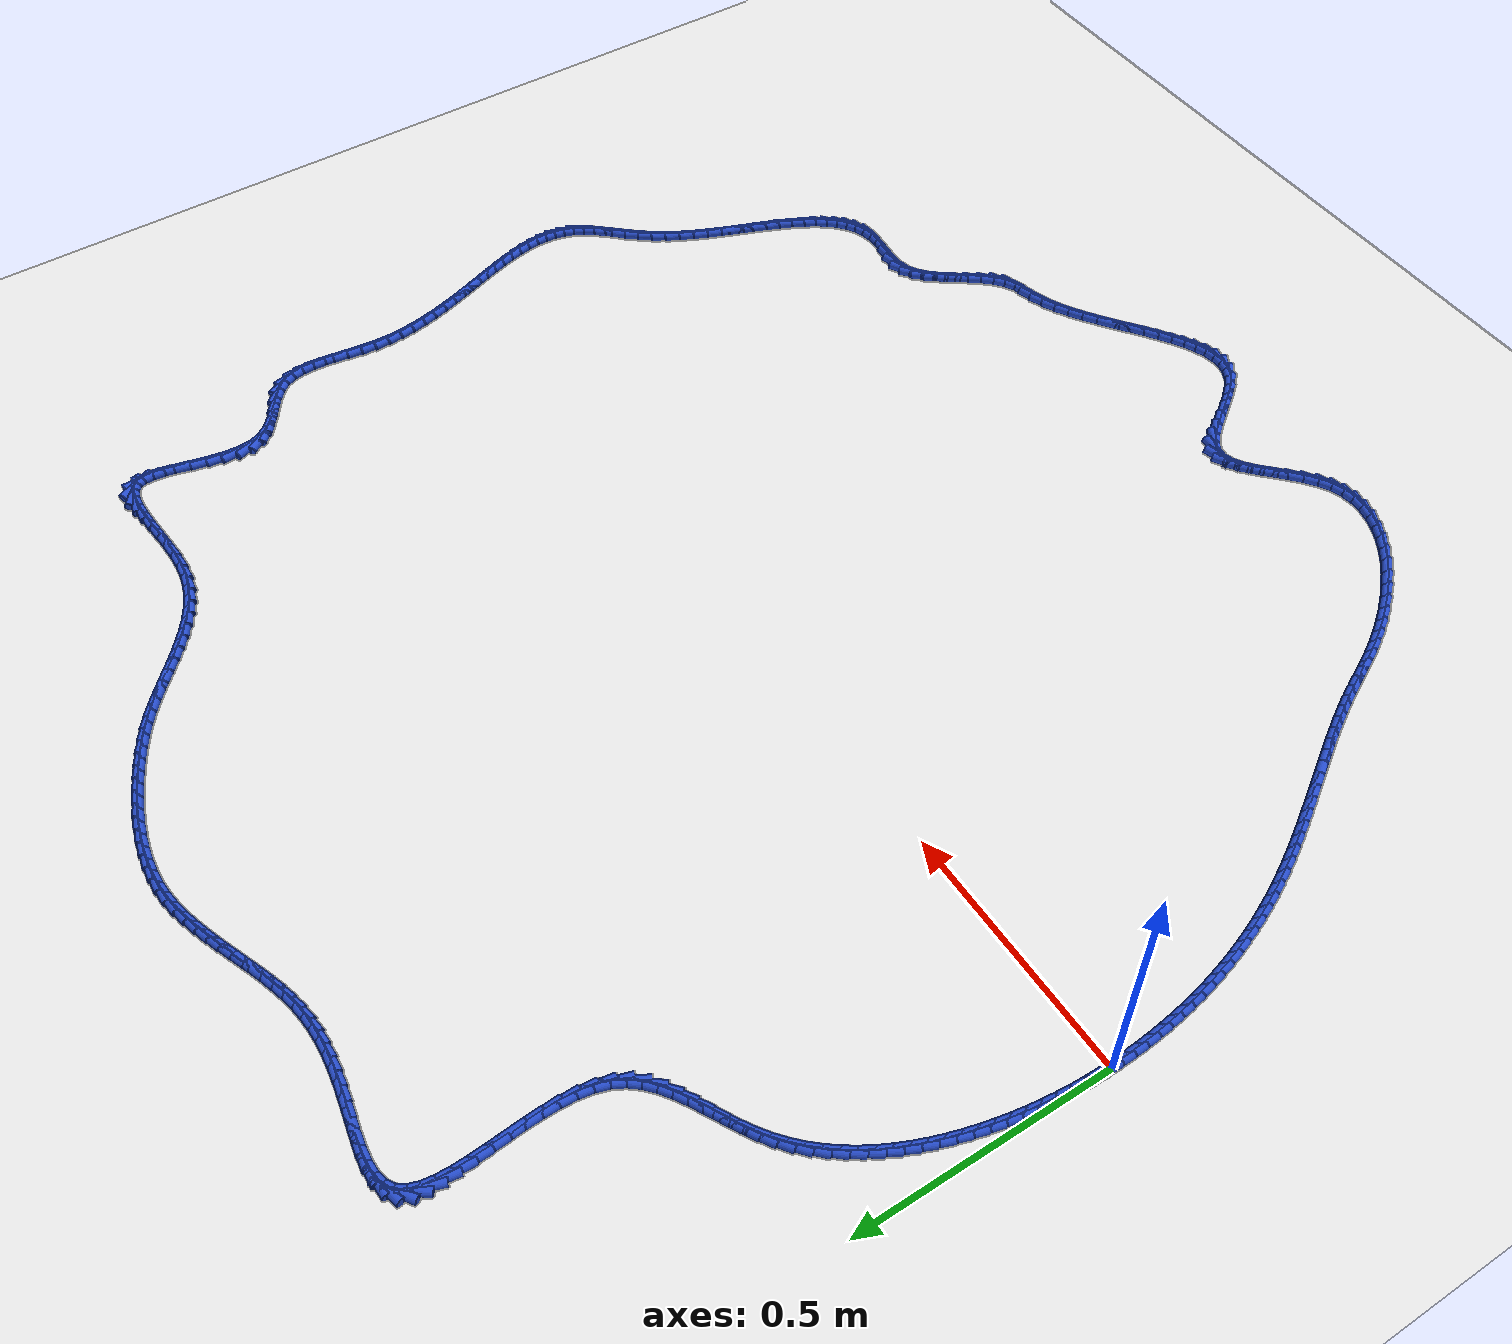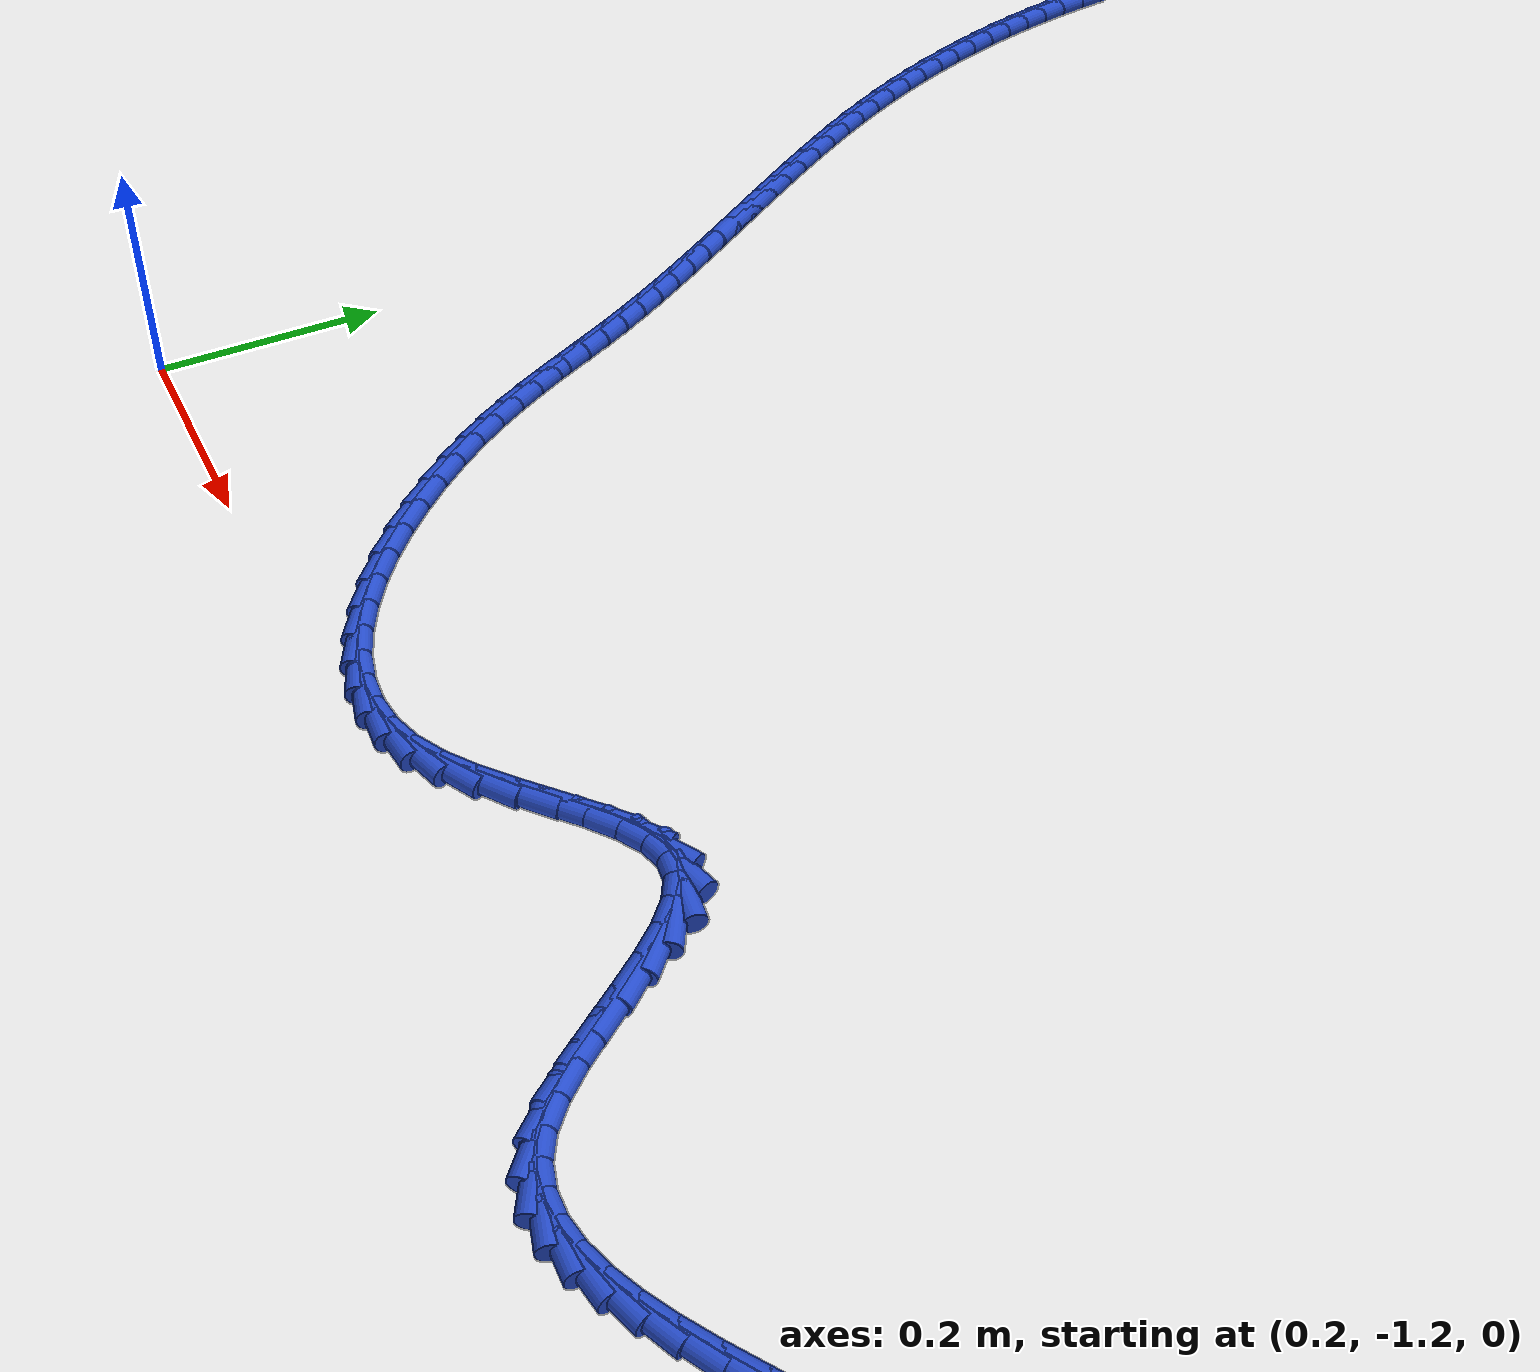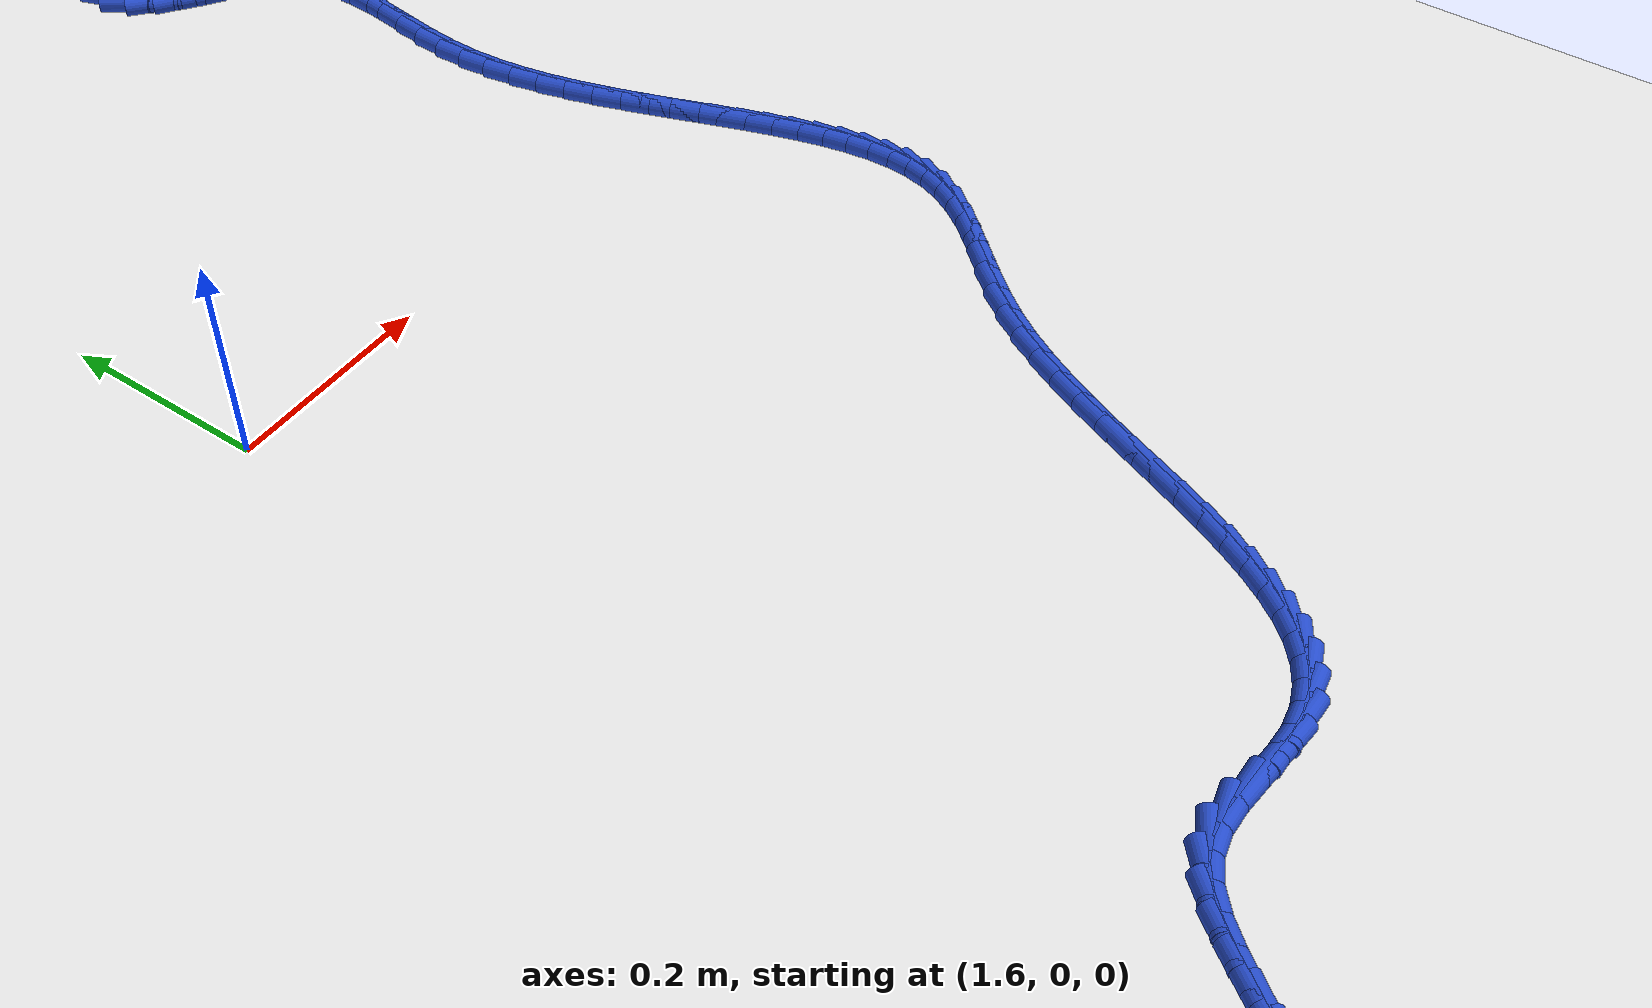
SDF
<sdf version="1.6">
 <world name="default">
  <light name="sun" type="directional">
   <pose>0 0 10 0 -0 0</pose>
   <diffuse>0.8 0.8 0.8 1</diffuse>
   <specular>0.2 0.2 0.2 1</specular>
   <attenuation>
    <range>1000</range>
    <constant>0.9</constant>
    <linear>0.01</linear>
    <quadratic>0.001</quadratic>
   </attenuation>
   <direction>-0.5 0.1 -0.9</direction>
  </light>
  <model name="ground_plane">
   <static>1</static>
   <link name="link">
    <collision name="collision">
     <geometry><plane><normal>0 0 1</normal><size>100 100</size></plane></geometry>
     <surface><friction><ode><mu>100</mu><mu2>50</mu2></ode></friction></surface>
    </collision>
    <visual name="visual">
     <cast_shadows>0</cast_shadows>
     <geometry><plane><normal>0 0 1</normal><size>100 100</size></plane></geometry>
     <material>
      <script><uri>file://media/materials/scripts/gazebo.material</uri><name>Gazebo/WhiteGlow</name></script>
     </material>
    </visual>
   </link>
  </model>
  <gravity>0 0 -9.8</gravity>
  <magnetic_field>6e-06 2.3e-05 -4.2e-05</magnetic_field>
  <atmosphere type="adiabatic"/>
  <physics name="default_physics" default="0" type="ode">
   <max_step_size>0.001</max_step_size>
   <real_time_factor>1</real_time_factor>
   <real_time_update_rate>1000</real_time_update_rate>
  </physics>
  <scene><ambient>0.4 0.4 0.4 1</ambient><background>0.7 0.7 0.7 1</background><shadows>1</shadows></scene>
  <spherical_coordinates>
   <surface_model>EARTH_WGS84</surface_model>
   <latitude_deg>0</latitude_deg>
   <longitude_deg>0</longitude_deg>
   <elevation>0</elevation>
   <heading_deg>0</heading_deg>
  </spherical_coordinates>
  <model name="line">
   <link name="link_0">
    <pose>8.673617379884035e-19 1.3877787807814457e-17 0.01 0 1.57 1.5621152291754117</pose>
    <collision name="collision">
     <geometry><cylinder><radius>0.01</radius><length>0.08</length></cylinder></geometry>
    </collision>
    <visual name="visual">
     <material>
      <script><name>Gazebo/Blue</name><uri>file://media/materials/scripts/gazebo.material</uri></script>
     </material>
     <geometry><cylinder><radius>0.01</radius><length>0.08</length></cylinder></geometry>
    </visual>
   </link>
   <link name="link_1">
    <pose>0.0002293132251595381 0.026414570452059822 0.01 0 1.57 1.5361049946007925</pose>
    <collision name="collision">
     <geometry><cylinder><radius>0.01</radius><length>0.08</length></cylinder></geometry>
    </collision>
    <visual name="visual">
     <material>
      <script><name>Gazebo/Blue</name><uri>file://media/materials/scripts/gazebo.material</uri></script>
     </material>
     <geometry><cylinder><radius>0.01</radius><length>0.08</length></cylinder></geometry>
    </visual>
   </link>
   <link name="link_2">
    <pose>0.0011446429842703087 0.05278895493053264 0.01 0 1.57 1.5092401439006613</pose>
    <collision name="collision">
     <geometry><cylinder><radius>0.01</radius><length>0.08</length></cylinder></geometry>
    </collision>
    <visual name="visual">
     <material>
      <script><name>Gazebo/Blue</name><uri>file://media/materials/scripts/gazebo.material</uri></script>
     </material>
     <geometry><cylinder><radius>0.01</radius><length>0.08</length></cylinder></geometry>
    </visual>
   </link>
   <link name="link_3">
    <pose>0.0027680820692032307 0.07912892596854929 0.01 0 1.57 1.48158026406147</pose>
    <collision name="collision">
     <geometry><cylinder><radius>0.01</radius><length>0.08</length></cylinder></geometry>
    </collision>
    <visual name="visual">
     <material>
      <script><name>Gazebo/Blue</name><uri>file://media/materials/scripts/gazebo.material</uri></script>
     </material>
     <geometry><cylinder><radius>0.01</radius><length>0.08</length></cylinder></geometry>
    </visual>
   </link>
   <link name="link_4">
    <pose>0.005121723271829229 0.10544025609924051 0.01 0 1.57 1.4531932485179575</pose>
    <collision name="collision">
     <geometry><cylinder><radius>0.01</radius><length>0.08</length></cylinder></geometry>
    </collision>
    <visual name="visual">
     <material>
      <script><name>Gazebo/Blue</name><uri>file://media/materials/scripts/gazebo.material</uri></script>
     </material>
     <geometry><cylinder><radius>0.01</radius><length>0.08</length></cylinder></geometry>
    </visual>
   </link>
   <link name="link_5">
    <pose>0.008227659384019221 0.13172871785573714 0.01 0 1.57 1.424154919011025</pose>
    <collision name="collision">
     <geometry><cylinder><radius>0.01</radius><length>0.08</length></cylinder></geometry>
    </collision>
    <visual name="visual">
     <material>
      <script><name>Gazebo/Blue</name><uri>file://media/materials/scripts/gazebo.material</uri></script>
     </material>
     <geometry><cylinder><radius>0.01</radius><length>0.08</length></cylinder></geometry>
    </visual>
   </link>
   <link name="link_6">
    <pose>0.012107983197644128 0.15800008377116992 0.01 0 1.57 1.3945484018601864</pose>
    <collision name="collision">
     <geometry><cylinder><radius>0.01</radius><length>0.08</length></cylinder></geometry>
    </collision>
    <visual name="visual">
     <material>
      <script><name>Gazebo/Blue</name><uri>file://media/materials/scripts/gazebo.material</uri></script>
     </material>
     <geometry><cylinder><radius>0.01</radius><length>0.08</length></cylinder></geometry>
    </visual>
   </link>
   <link name="link_7">
    <pose>0.016784787504574874 0.18426012637866962 0.01 0 1.57 1.3644632593502504</pose>
    <collision name="collision">
     <geometry><cylinder><radius>0.01</radius><length>0.08</length></cylinder></geometry>
    </collision>
    <visual name="visual">
     <material>
      <script><name>Gazebo/Blue</name><uri>file://media/materials/scripts/gazebo.material</uri></script>
     </material>
     <geometry><cylinder><radius>0.01</radius><length>0.08</length></cylinder></geometry>
    </visual>
   </link>
   <link name="link_8">
    <pose>0.02228016509668238 0.21051461821136716 0.01 0 1.57 1.3339274144078819</pose>
    <collision name="collision">
     <geometry><cylinder><radius>0.01</radius><length>0.08</length></cylinder></geometry>
    </collision>
    <visual name="visual">
     <material>
      <script><name>Gazebo/Blue</name><uri>file://media/materials/scripts/gazebo.material</uri></script>
     </material>
     <geometry><cylinder><radius>0.01</radius><length>0.08</length></cylinder></geometry>
    </visual>
   </link>
   <link name="link_9">
    <pose>0.02861723554550145 0.23676587650979158 0.01 0 1.57 1.3017008043184863</pose>
    <collision name="collision">
     <geometry><cylinder><radius>0.01</radius><length>0.08</length></cylinder></geometry>
    </collision>
    <visual name="visual">
     <material>
      <script><name>Gazebo/Blue</name><uri>file://media/materials/scripts/gazebo.material</uri></script>
     </material>
     <geometry><cylinder><radius>0.01</radius><length>0.08</length></cylinder></geometry>
    </visual>
   </link>
   <link name="link_10">
    <pose>0.03583859797094577 0.26295066643766024 0.01 0 1.57 1.2664476155806226</pose>
    <collision name="collision">
     <geometry><cylinder><radius>0.01</radius><length>0.08</length></cylinder></geometry>
    </collision>
    <visual name="visual">
     <material>
      <script><name>Gazebo/Blue</name><uri>file://media/materials/scripts/gazebo.material</uri></script>
     </material>
     <geometry><cylinder><radius>0.01</radius><length>0.08</length></cylinder></geometry>
    </visual>
   </link>
   <link name="link_11">
    <pose>0.04400427736551788 0.2889471120589975 0.01 0 1.57 1.227851036137061</pose>
    <collision name="collision">
     <geometry><cylinder><radius>0.01</radius><length>0.08</length></cylinder></geometry>
    </collision>
    <visual name="visual">
     <material>
      <script><name>Gazebo/Blue</name><uri>file://media/materials/scripts/gazebo.material</uri></script>
     </material>
     <geometry><cylinder><radius>0.01</radius><length>0.08</length></cylinder></geometry>
    </visual>
   </link>
   <link name="link_12">
    <pose>0.05317491316743572 0.31463126972085853 0.01 0 1.57 1.185618888573758</pose>
    <collision name="collision">
     <geometry><cylinder><radius>0.01</radius><length>0.08</length></cylinder></geometry>
    </collision>
    <visual name="visual">
     <material>
      <script><name>Gazebo/Blue</name><uri>file://media/materials/scripts/gazebo.material</uri></script>
     </material>
     <geometry><cylinder><radius>0.01</radius><length>0.08</length></cylinder></geometry>
    </visual>
   </link>
   <link name="link_13">
    <pose>0.06341114481491726 0.3398791957702987 0.01 0 1.57 1.1394536189883473</pose>
    <collision name="collision">
     <geometry><cylinder><radius>0.01</radius><length>0.08</length></cylinder></geometry>
    </collision>
    <visual name="visual">
     <material>
      <script><name>Gazebo/Blue</name><uri>file://media/materials/scripts/gazebo.material</uri></script>
     </material>
     <geometry><cylinder><radius>0.01</radius><length>0.08</length></cylinder></geometry>
    </visual>
   </link>
   <link name="link_14">
    <pose>0.07477361174618043 0.3645669465543732 0.01 0 1.57 1.0890675836702062</pose>
    <collision name="collision">
     <geometry><cylinder><radius>0.01</radius><length>0.08</length></cylinder></geometry>
    </collision>
    <visual name="visual">
     <material>
      <script><name>Gazebo/Blue</name><uri>file://media/materials/scripts/gazebo.material</uri></script>
     </material>
     <geometry><cylinder><radius>0.01</radius><length>0.08</length></cylinder></geometry>
    </visual>
   </link>
   <link name="link_15">
    <pose>0.08732295339944318 0.3885705784201373 0.01 0 1.57 1.034204950976809</pose>
    <collision name="collision">
     <geometry><cylinder><radius>0.01</radius><length>0.08</length></cylinder></geometry>
    </collision>
    <visual name="visual">
     <material>
      <script><name>Gazebo/Blue</name><uri>file://media/materials/scripts/gazebo.material</uri></script>
     </material>
     <geometry><cylinder><radius>0.01</radius><length>0.08</length></cylinder></geometry>
    </visual>
   </link>
   <link name="link_16">
    <pose>0.10111980921292348 0.4117661477146463 0.01 0 1.57 0.9746712591551953</pose>
    <collision name="collision">
     <geometry><cylinder><radius>0.01</radius><length>0.08</length></cylinder></geometry>
    </collision>
    <visual name="visual">
     <material>
      <script><name>Gazebo/Blue</name><uri>file://media/materials/scripts/gazebo.material</uri></script>
     </material>
     <geometry><cylinder><radius>0.01</radius><length>0.08</length></cylinder></geometry>
    </visual>
   </link>
   <link name="link_17">
    <pose>0.11622481862483927 0.4340297107849556 0.01 0 1.57 0.910370661110897</pose>
    <collision name="collision">
     <geometry><cylinder><radius>0.01</radius><length>0.08</length></cylinder></geometry>
    </collision>
    <visual name="visual">
     <material>
      <script><name>Gazebo/Blue</name><uri>file://media/materials/scripts/gazebo.material</uri></script>
     </material>
     <geometry><cylinder><radius>0.01</radius><length>0.08</length></cylinder></geometry>
    </visual>
   </link>
   <link name="link_18">
    <pose>0.13269862107340843 0.4552373239781201 0.01 0 1.57 0.8413489667854219</pose>
    <collision name="collision">
     <geometry><cylinder><radius>0.01</radius><length>0.08</length></cylinder></geometry>
    </collision>
    <visual name="visual">
     <material>
      <script><name>Gazebo/Blue</name><uri>file://media/materials/scripts/gazebo.material</uri></script>
     </material>
     <geometry><cylinder><radius>0.01</radius><length>0.08</length></cylinder></geometry>
    </visual>
   </link>
   <link name="link_19">
    <pose>0.150601855996849 0.4752650436411953 0.01 0 1.57 0.767837699025177</pose>
    <collision name="collision">
     <geometry><cylinder><radius>0.01</radius><length>0.08</length></cylinder></geometry>
    </collision>
    <visual name="visual">
     <material>
      <script><name>Gazebo/Blue</name><uri>file://media/materials/scripts/gazebo.material</uri></script>
     </material>
     <geometry><cylinder><radius>0.01</radius><length>0.08</length></cylinder></geometry>
    </visual>
   </link>
   <link name="link_20">
    <pose>0.1699951628333789 0.4939889261212365 0.01 0 1.57 0.6902909568805675</pose>
    <collision name="collision">
     <geometry><cylinder><radius>0.01</radius><length>0.08</length></cylinder></geometry>
    </collision>
    <visual name="visual">
     <material>
      <script><name>Gazebo/Blue</name><uri>file://media/materials/scripts/gazebo.material</uri></script>
     </material>
     <geometry><cylinder><radius>0.01</radius><length>0.08</length></cylinder></geometry>
    </visual>
   </link>
   <link name="link_21">
    <pose>0.19093918102121613 0.5112850277652989 0.01 0 1.57 0.6096205533574776</pose>
    <collision name="collision">
     <geometry><cylinder><radius>0.01</radius><length>0.08</length></cylinder></geometry>
    </collision>
    <visual name="visual">
     <material>
      <script><name>Gazebo/Blue</name><uri>file://media/materials/scripts/gazebo.material</uri></script>
     </material>
     <geometry><cylinder><radius>0.01</radius><length>0.08</length></cylinder></geometry>
    </visual>
   </link>
   <link name="link_22">
    <pose>0.21349014319490003 0.5270335871475053 0.01 0 1.57 0.5391576238009415</pose>
    <collision name="collision">
     <geometry><cylinder><radius>0.01</radius><length>0.08</length></cylinder></geometry>
    </collision>
    <visual name="visual">
     <material>
      <script><name>Gazebo/Blue</name><uri>file://media/materials/scripts/gazebo.material</uri></script>
     </material>
     <geometry><cylinder><radius>0.01</radius><length>0.08</length></cylinder></geometry>
    </visual>
   </link>
   <link name="link_23">
    <pose>0.2374420848625966 0.5413636780520171 0.01 0 1.57 0.49715278975836</pose>
    <collision name="collision">
     <geometry><cylinder><radius>0.01</radius><length>0.08</length></cylinder></geometry>
    </collision>
    <visual name="visual">
     <material>
      <script><name>Gazebo/Blue</name><uri>file://media/materials/scripts/gazebo.material</uri></script>
     </material>
     <geometry><cylinder><radius>0.01</radius><length>0.08</length></cylinder></geometry>
    </visual>
   </link>
   <link name="link_24">
    <pose>0.26218390229287947 0.5547888670649314 0.01 0 1.57 0.48350048736273726</pose>
    <collision name="collision">
     <geometry><cylinder><radius>0.01</radius><length>0.08</length></cylinder></geometry>
    </collision>
    <visual name="visual">
     <material>
      <script><name>Gazebo/Blue</name><uri>file://media/materials/scripts/gazebo.material</uri></script>
     </material>
     <geometry><cylinder><radius>0.01</radius><length>0.08</length></cylinder></geometry>
    </visual>
   </link>
   <link name="link_25">
    <pose>0.2870697886501498 0.5678556553599021 0.01 0 1.57 0.49790572403119704</pose>
    <collision name="collision">
     <geometry><cylinder><radius>0.01</radius><length>0.08</length></cylinder></geometry>
    </collision>
    <visual name="visual">
     <material>
      <script><name>Gazebo/Blue</name><uri>file://media/materials/scripts/gazebo.material</uri></script>
     </material>
     <geometry><cylinder><radius>0.01</radius><length>0.08</length></cylinder></geometry>
    </visual>
   </link>
   <link name="link_26">
    <pose>0.3114539370988087 0.5811105441105839 0.01 0 1.57 0.5419221140527369</pose>
    <collision name="collision">
     <geometry><cylinder><radius>0.01</radius><length>0.08</length></cylinder></geometry>
    </collision>
    <visual name="visual">
     <material>
      <script><name>Gazebo/Blue</name><uri>file://media/materials/scripts/gazebo.material</uri></script>
     </material>
     <geometry><cylinder><radius>0.01</radius><length>0.08</length></cylinder></geometry>
    </visual>
   </link>
   <link name="link_27">
    <pose>0.334690540803257 0.5951000344906303 0.01 0 1.57 0.6188270970532647</pose>
    <collision name="collision">
     <geometry><cylinder><radius>0.01</radius><length>0.08</length></cylinder></geometry>
    </collision>
    <visual name="visual">
     <material>
      <script><name>Gazebo/Blue</name><uri>file://media/materials/scripts/gazebo.material</uri></script>
     </material>
     <geometry><cylinder><radius>0.01</radius><length>0.08</length></cylinder></geometry>
    </visual>
   </link>
   <link name="link_28">
    <pose>0.3561337929278963 0.6103706276736961 0.01 0 1.57 0.7326555558644336</pose>
    <collision name="collision">
     <geometry><cylinder><radius>0.01</radius><length>0.08</length></cylinder></geometry>
    </collision>
    <visual name="visual">
     <material>
      <script><name>Gazebo/Blue</name><uri>file://media/materials/scripts/gazebo.material</uri></script>
     </material>
     <geometry><cylinder><radius>0.01</radius><length>0.08</length></cylinder></geometry>
    </visual>
   </link>
   <link name="link_29">
    <pose>0.3751378866371274 0.627468824833435 0.01 0 1.57 0.8854593208021324</pose>
    <collision name="collision">
     <geometry><cylinder><radius>0.01</radius><length>0.08</length></cylinder></geometry>
    </collision>
    <visual name="visual">
     <material>
      <script><name>Gazebo/Blue</name><uri>file://media/materials/scripts/gazebo.material</uri></script>
     </material>
     <geometry><cylinder><radius>0.01</radius><length>0.08</length></cylinder></geometry>
    </visual>
   </link>
   <link name="link_30">
    <pose>0.3910570150953514 0.6469411271435013 0.01 0 1.57 1.0722695040322578</pose>
    <collision name="collision">
     <geometry><cylinder><radius>0.01</radius><length>0.08</length></cylinder></geometry>
    </collision>
    <visual name="visual">
     <material>
      <script><name>Gazebo/Blue</name><uri>file://media/materials/scripts/gazebo.material</uri></script>
     </material>
     <geometry><cylinder><radius>0.01</radius><length>0.08</length></cylinder></geometry>
    </visual>
   </link>
   <link name="link_31">
    <pose>0.403246814643812 0.669332745311993 0.01 0 1.57 1.260851132319361</pose>
    <collision name="collision">
     <geometry><cylinder><radius>0.01</radius><length>0.08</length></cylinder></geometry>
    </collision>
    <visual name="visual">
     <material>
      <script><name>Gazebo/Blue</name><uri>file://media/materials/scripts/gazebo.material</uri></script>
     </material>
     <geometry><cylinder><radius>0.01</radius><length>0.08</length></cylinder></geometry>
    </visual>
   </link>
   <link name="link_32">
    <pose>0.4114242190296432 0.6948658237087181 0.01 0 1.57 1.4047687014745058</pose>
    <collision name="collision">
     <geometry><cylinder><radius>0.01</radius><length>0.08</length></cylinder></geometry>
    </collision>
    <visual name="visual">
     <material>
      <script><name>Gazebo/Blue</name><uri>file://media/materials/scripts/gazebo.material</uri></script>
     </material>
     <geometry><cylinder><radius>0.01</radius><length>0.08</length></cylinder></geometry>
    </visual>
   </link>
   <link name="link_33">
    <pose>0.41614130437089386 0.723015735806926 0.01 0 1.57 1.5069587871187897</pose>
    <collision name="collision">
     <geometry><cylinder><radius>0.01</radius><length>0.08</length></cylinder></geometry>
    </collision>
    <visual name="visual">
     <material>
      <script><name>Gazebo/Blue</name><uri>file://media/materials/scripts/gazebo.material</uri></script>
     </material>
     <geometry><cylinder><radius>0.01</radius><length>0.08</length></cylinder></geometry>
    </visual>
   </link>
   <link name="link_34">
    <pose>0.41806778920462034 0.7531526611180042 0.01 0 1.57 -1.5646239149254952</pose>
    <collision name="collision">
     <geometry><cylinder><radius>0.01</radius><length>0.08</length></cylinder></geometry>
    </collision>
    <visual name="visual">
     <material>
      <script><name>Gazebo/Blue</name><uri>file://media/materials/scripts/gazebo.material</uri></script>
     </material>
     <geometry><cylinder><radius>0.01</radius><length>0.08</length></cylinder></geometry>
    </visual>
   </link>
   <link name="link_35">
    <pose>0.4178733920678791 0.7846467791533396 0.01 0 1.57 -1.5197703762544845</pose>
    <collision name="collision">
     <geometry><cylinder><radius>0.01</radius><length>0.08</length></cylinder></geometry>
    </collision>
    <visual name="visual">
     <material>
      <script><name>Gazebo/Blue</name><uri>file://media/materials/scripts/gazebo.material</uri></script>
     </material>
     <geometry><cylinder><radius>0.01</radius><length>0.08</length></cylinder></geometry>
    </visual>
   </link>
   <link name="link_36">
    <pose>0.41622783149772635 0.8168682694243189 0.01 0 1.57 -1.495841795573981</pose>
    <collision name="collision">
     <geometry><cylinder><radius>0.01</radius><length>0.08</length></cylinder></geometry>
    </collision>
    <visual name="visual">
     <material>
      <script><name>Gazebo/Blue</name><uri>file://media/materials/scripts/gazebo.material</uri></script>
     </material>
     <geometry><cylinder><radius>0.01</radius><length>0.08</length></cylinder></geometry>
    </visual>
   </link>
   <link name="link_37">
    <pose>0.41380082603121865 0.8491873114423301 0.01 0 1.57 -1.4910979463703196</pose>
    <collision name="collision">
     <geometry><cylinder><radius>0.01</radius><length>0.08</length></cylinder></geometry>
    </collision>
    <visual name="visual">
     <material>
      <script><name>Gazebo/Blue</name><uri>file://media/materials/scripts/gazebo.material</uri></script>
     </material>
     <geometry><cylinder><radius>0.01</radius><length>0.08</length></cylinder></geometry>
    </visual>
   </link>
   <link name="link_38">
    <pose>0.41126209420541204 0.8809740847187592 0.01 0 1.57 -1.506208408278429</pose>
    <collision name="collision">
     <geometry><cylinder><radius>0.01</radius><length>0.08</length></cylinder></geometry>
    </collision>
    <visual name="visual">
     <material>
      <script><name>Gazebo/Blue</name><uri>file://media/materials/scripts/gazebo.material</uri></script>
     </material>
     <geometry><cylinder><radius>0.01</radius><length>0.08</length></cylinder></geometry>
    </visual>
   </link>
   <link name="link_39">
    <pose>0.4092813545573631 0.9115987687649938 0.01 0 1.57 -1.544685145814048</pose>
    <collision name="collision">
     <geometry><cylinder><radius>0.01</radius><length>0.08</length></cylinder></geometry>
    </collision>
    <visual name="visual">
     <material>
      <script><name>Gazebo/Blue</name><uri>file://media/materials/scripts/gazebo.material</uri></script>
     </material>
     <geometry><cylinder><radius>0.01</radius><length>0.08</length></cylinder></geometry>
    </visual>
   </link>
   <link name="link_40">
    <pose>0.40852832562412816 0.9404315430924213 0.01 0 1.57 1.5274930439973453</pose>
    <collision name="collision">
     <geometry><cylinder><radius>0.01</radius><length>0.08</length></cylinder></geometry>
    </collision>
    <visual name="visual">
     <material>
      <script><name>Gazebo/Blue</name><uri>file://media/materials/scripts/gazebo.material</uri></script>
     </material>
     <geometry><cylinder><radius>0.01</radius><length>0.08</length></cylinder></geometry>
    </visual>
   </link>
   <link name="link_41">
    <pose>0.4096727259427635 0.966842587212428 0.01 0 1.57 1.413225290394191</pose>
    <collision name="collision">
     <geometry><cylinder><radius>0.01</radius><length>0.08</length></cylinder></geometry>
    </collision>
    <visual name="visual">
     <material>
      <script><name>Gazebo/Blue</name><uri>file://media/materials/scripts/gazebo.material</uri></script>
     </material>
     <geometry><cylinder><radius>0.01</radius><length>0.08</length></cylinder></geometry>
    </visual>
   </link>
   <link name="link_42">
    <pose>0.4133842740503254 0.9902020806364011 0.01 0 1.57 1.231359349624539</pose>
    <collision name="collision">
     <geometry><cylinder><radius>0.01</radius><length>0.08</length></cylinder></geometry>
    </collision>
    <visual name="visual">
     <material>
      <script><name>Gazebo/Blue</name><uri>file://media/materials/scripts/gazebo.material</uri></script>
     </material>
     <geometry><cylinder><radius>0.01</radius><length>0.08</length></cylinder></geometry>
    </visual>
   </link>
   <link name="link_43">
    <pose>0.4203326884838704 1.0098802028757285 0.01 0 1.57 0.9557966648315243</pose>
    <collision name="collision">
     <geometry><cylinder><radius>0.01</radius><length>0.08</length></cylinder></geometry>
    </collision>
    <visual name="visual">
     <material>
      <script><name>Gazebo/Blue</name><uri>file://media/materials/scripts/gazebo.material</uri></script>
     </material>
     <geometry><cylinder><radius>0.01</radius><length>0.08</length></cylinder></geometry>
    </visual>
   </link>
   <link name="link_44">
    <pose>0.4311876877804547 1.0252471334417965 0.01 0 1.57 0.5942304757525863</pose>
    <collision name="collision">
     <geometry><cylinder><radius>0.01</radius><length>0.08</length></cylinder></geometry>
    </collision>
    <visual name="visual">
     <material>
      <script><name>Gazebo/Blue</name><uri>file://media/materials/scripts/gazebo.material</uri></script>
     </material>
     <geometry><cylinder><radius>0.01</radius><length>0.08</length></cylinder></geometry>
    </visual>
   </link>
   <link name="link_45">
    <pose>0.4466183786808957 1.0356736529023942 0.01 0 1.57 0.25399072506424514</pose>
    <collision name="collision">
     <geometry><cylinder><radius>0.01</radius><length>0.08</length></cylinder></geometry>
    </collision>
    <visual name="visual">
     <material>
      <script><name>Gazebo/Blue</name><uri>file://media/materials/scripts/gazebo.material</uri></script>
     </material>
     <geometry><cylinder><radius>0.01</radius><length>0.08</length></cylinder></geometry>
    </visual>
   </link>
   <link name="link_46">
    <pose>0.46688292376191853 1.0409342720295538 0.01 0 1.57 0.04013133042125194</pose>
    <collision name="collision">
     <geometry><cylinder><radius>0.01</radius><length>0.08</length></cylinder></geometry>
    </collision>
    <visual name="visual">
     <material>
      <script><name>Gazebo/Blue</name><uri>file://media/materials/scripts/gazebo.material</uri></script>
     </material>
     <geometry><cylinder><radius>0.01</radius><length>0.08</length></cylinder></geometry>
    </visual>
   </link>
   <link name="link_47">
    <pose>0.4911159655974157 1.0419072986554676 0.01 0 1.57 -0.08267206849056742</pose>
    <collision name="collision">
     <geometry><cylinder><radius>0.01</radius><length>0.08</length></cylinder></geometry>
    </collision>
    <visual name="visual">
     <material>
      <script><name>Gazebo/Blue</name><uri>file://media/materials/scripts/gazebo.material</uri></script>
     </material>
     <geometry><cylinder><radius>0.01</radius><length>0.08</length></cylinder></geometry>
    </visual>
   </link>
   <link name="link_48">
    <pose>0.5182618848717185 1.03965796253079 0.01 0 1.57 -0.1507774937795021</pose>
    <collision name="collision">
     <geometry><cylinder><radius>0.01</radius><length>0.08</length></cylinder></geometry>
    </collision>
    <visual name="visual">
     <material>
      <script><name>Gazebo/Blue</name><uri>file://media/materials/scripts/gazebo.material</uri></script>
     </material>
     <geometry><cylinder><radius>0.01</radius><length>0.08</length></cylinder></geometry>
    </visual>
   </link>
   <link name="link_49">
    <pose>0.5472650622691572 1.0352514934061745 0.01 0 1.57 -0.182428274732098</pose>
    <collision name="collision">
     <geometry><cylinder><radius>0.01</radius><length>0.08</length></cylinder></geometry>
    </collision>
    <visual name="visual">
     <material>
      <script><name>Gazebo/Blue</name><uri>file://media/materials/scripts/gazebo.material</uri></script>
     </material>
     <geometry><cylinder><radius>0.01</radius><length>0.08</length></cylinder></geometry>
    </visual>
   </link>
   <link name="link_50">
    <pose>0.5770698784740633 1.029753121032276 0.01 0 1.57 -0.18483875823163884</pose>
    <collision name="collision">
     <geometry><cylinder><radius>0.01</radius><length>0.08</length></cylinder></geometry>
    </collision>
    <visual name="visual">
     <material>
      <script><name>Gazebo/Blue</name><uri>file://media/materials/scripts/gazebo.material</uri></script>
     </material>
     <geometry><cylinder><radius>0.01</radius><length>0.08</length></cylinder></geometry>
    </visual>
   </link>
   <link name="link_51">
    <pose>0.6066210005369806 1.0242278603505293 0.01 0 1.57 -0.16321358004310377</pose>
    <collision name="collision">
     <geometry><cylinder><radius>0.01</radius><length>0.08</length></cylinder></geometry>
    </collision>
    <visual name="visual">
     <material>
      <script><name>Gazebo/Blue</name><uri>file://media/materials/scripts/gazebo.material</uri></script>
     </material>
     <geometry><cylinder><radius>0.01</radius><length>0.08</length></cylinder></geometry>
    </visual>
   </link>
   <link name="link_52">
    <pose>0.6351427653393129 1.0195309401793358 0.01 0 1.57 -0.13062801544047986</pose>
    <collision name="collision">
     <geometry><cylinder><radius>0.01</radius><length>0.08</length></cylinder></geometry>
    </collision>
    <visual name="visual">
     <material>
      <script><name>Gazebo/Blue</name><uri>file://media/materials/scripts/gazebo.material</uri></script>
     </material>
     <geometry><cylinder><radius>0.01</radius><length>0.08</length></cylinder></geometry>
    </visual>
   </link>
   <link name="link_53">
    <pose>0.6626620887552457 1.0159155582391808 0.01 0 1.57 -0.089243317171403</pose>
    <collision name="collision">
     <geometry><cylinder><radius>0.01</radius><length>0.08</length></cylinder></geometry>
    </collision>
    <visual name="visual">
     <material>
      <script><name>Gazebo/Blue</name><uri>file://media/materials/scripts/gazebo.material</uri></script>
     </material>
     <geometry><cylinder><radius>0.01</radius><length>0.08</length></cylinder></geometry>
    </visual>
   </link>
   <link name="link_54">
    <pose>0.6893489593583562 1.0135275904603351 0.01 0 1.57 -0.03896972625812718</pose>
    <collision name="collision">
     <geometry><cylinder><radius>0.01</radius><length>0.08</length></cylinder></geometry>
    </collision>
    <visual name="visual">
     <material>
      <script><name>Gazebo/Blue</name><uri>file://media/materials/scripts/gazebo.material</uri></script>
     </material>
     <geometry><cylinder><radius>0.01</radius><length>0.08</length></cylinder></geometry>
    </visual>
   </link>
   <link name="link_55">
    <pose>0.7153733657222208 1.0125129127730679 0.01 0 1.57 0.019756543340623465</pose>
    <collision name="collision">
     <geometry><cylinder><radius>0.01</radius><length>0.08</length></cylinder></geometry>
    </collision>
    <visual name="visual">
     <material>
      <script><name>Gazebo/Blue</name><uri>file://media/materials/scripts/gazebo.material</uri></script>
     </material>
     <geometry><cylinder><radius>0.01</radius><length>0.08</length></cylinder></geometry>
    </visual>
   </link>
   <link name="link_56">
    <pose>0.7409052964204158 1.0130174011076492 0.01 0 1.57 0.08584869576111889</pose>
    <collision name="collision">
     <geometry><cylinder><radius>0.01</radius><length>0.08</length></cylinder></geometry>
    </collision>
    <visual name="visual">
     <material>
      <script><name>Gazebo/Blue</name><uri>file://media/materials/scripts/gazebo.material</uri></script>
     </material>
     <geometry><cylinder><radius>0.01</radius><length>0.08</length></cylinder></geometry>
    </visual>
   </link>
   <link name="link_57">
    <pose>0.766114740026518 1.0151869313943487 0.01 0 1.57 0.15749196918500613</pose>
    <collision name="collision">
     <geometry><cylinder><radius>0.01</radius><length>0.08</length></cylinder></geometry>
    </collision>
    <visual name="visual">
     <material>
      <script><name>Gazebo/Blue</name><uri>file://media/materials/scripts/gazebo.material</uri></script>
     </material>
     <geometry><cylinder><radius>0.01</radius><length>0.08</length></cylinder></geometry>
    </visual>
   </link>
   <link name="link_58">
    <pose>0.7911712703358393 1.0191660875160948 0.01 0 1.57 0.22706755578521565</pose>
    <collision name="collision">
     <geometry><cylinder><radius>0.01</radius><length>0.08</length></cylinder></geometry>
    </collision>
    <visual name="visual">
     <material>
      <script><name>Gazebo/Blue</name><uri>file://media/materials/scripts/gazebo.material</uri></script>
     </material>
     <geometry><cylinder><radius>0.01</radius><length>0.08</length></cylinder></geometry>
    </visual>
   </link>
   <link name="link_59">
    <pose>0.8161958656858561 1.0249480769758832 0.01 0 1.57 0.28339389213689253</pose>
    <collision name="collision">
     <geometry><cylinder><radius>0.01</radius><length>0.08</length></cylinder></geometry>
    </collision>
    <visual name="visual">
     <material>
      <script><name>Gazebo/Blue</name><uri>file://media/materials/scripts/gazebo.material</uri></script>
     </material>
     <geometry><cylinder><radius>0.01</radius><length>0.08</length></cylinder></geometry>
    </visual>
   </link>
   <link name="link_60">
    <pose>0.8412159695468947 1.0322347432230126 0.01 0 1.57 0.3259129243356896</pose>
    <collision name="collision">
     <geometry><cylinder><radius>0.01</radius><length>0.08</length></cylinder></geometry>
    </collision>
    <visual name="visual">
     <material>
      <script><name>Gazebo/Blue</name><uri>file://media/materials/scripts/gazebo.material</uri></script>
     </material>
     <geometry><cylinder><radius>0.01</radius><length>0.08</length></cylinder></geometry>
    </visual>
   </link>
   <link name="link_61">
    <pose>0.8662483957931252 1.040694818180352 0.01 0 1.57 0.3554126896417086</pose>
    <collision name="collision">
     <geometry><cylinder><radius>0.01</radius><length>0.08</length></cylinder></geometry>
    </collision>
    <visual name="visual">
     <material>
      <script><name>Gazebo/Blue</name><uri>file://media/materials/scripts/gazebo.material</uri></script>
     </material>
     <geometry><cylinder><radius>0.01</radius><length>0.08</length></cylinder></geometry>
    </visual>
   </link>
   <link name="link_62">
    <pose>0.8913099582987158 1.0499970337707702 0.01 0 1.57 0.37258731606013756</pose>
    <collision name="collision">
     <geometry><cylinder><radius>0.01</radius><length>0.08</length></cylinder></geometry>
    </collision>
    <visual name="visual">
     <material>
      <script><name>Gazebo/Blue</name><uri>file://media/materials/scripts/gazebo.material</uri></script>
     </material>
     <geometry><cylinder><radius>0.01</radius><length>0.08</length></cylinder></geometry>
    </visual>
   </link>
   <link name="link_63">
    <pose>0.9164174709378362 1.0598101219171359 0.01 0 1.57 0.37792068263176093</pose>
    <collision name="collision">
     <geometry><cylinder><radius>0.01</radius><length>0.08</length></cylinder></geometry>
    </collision>
    <visual name="visual">
     <material>
      <script><name>Gazebo/Blue</name><uri>file://media/materials/scripts/gazebo.material</uri></script>
     </material>
     <geometry><cylinder><radius>0.01</radius><length>0.08</length></cylinder></geometry>
    </visual>
   </link>
   <link name="link_64">
    <pose>0.941587747584655 1.0698028145423184 0.01 0 1.57 0.37163556123159014</pose>
    <collision name="collision">
     <geometry><cylinder><radius>0.01</radius><length>0.08</length></cylinder></geometry>
    </collision>
    <visual name="visual">
     <material>
      <script><name>Gazebo/Blue</name><uri>file://media/materials/scripts/gazebo.material</uri></script>
     </material>
     <geometry><cylinder><radius>0.01</radius><length>0.08</length></cylinder></geometry>
    </visual>
   </link>
   <link name="link_65">
    <pose>0.9668376021133415 1.0796438435691862 0.01 0 1.57 0.3536852074107787</pose>
    <collision name="collision">
     <geometry><cylinder><radius>0.01</radius><length>0.08</length></cylinder></geometry>
    </collision>
    <visual name="visual">
     <material>
      <script><name>Gazebo/Blue</name><uri>file://media/materials/scripts/gazebo.material</uri></script>
     </material>
     <geometry><cylinder><radius>0.01</radius><length>0.08</length></cylinder></geometry>
    </visual>
   </link>
   <link name="link_66">
    <pose>0.9921838483980653 1.0890019409206082 0.01 0 1.57 0.3237787700720862</pose>
    <collision name="collision">
     <geometry><cylinder><radius>0.01</radius><length>0.08</length></cylinder></geometry>
    </collision>
    <visual name="visual">
     <material>
      <script><name>Gazebo/Blue</name><uri>file://media/materials/scripts/gazebo.material</uri></script>
     </material>
     <geometry><cylinder><radius>0.01</radius><length>0.08</length></cylinder></geometry>
    </visual>
   </link>
   <link name="link_67">
    <pose>1.0176433003129945 1.0975458385194532 0.01 0 1.57 0.2814455624364506</pose>
    <collision name="collision">
     <geometry><cylinder><radius>0.01</radius><length>0.08</length></cylinder></geometry>
    </collision>
    <visual name="visual">
     <material>
      <script><name>Gazebo/Blue</name><uri>file://media/materials/scripts/gazebo.material</uri></script>
     </material>
     <geometry><cylinder><radius>0.01</radius><length>0.08</length></cylinder></geometry>
    </visual>
   </link>
   <link name="link_68">
    <pose>1.0432327717322996 1.1049442682885906 0.01 0 1.57 0.2261548790015328</pose>
    <collision name="collision">
     <geometry><cylinder><radius>0.01</radius><length>0.08</length></cylinder></geometry>
    </collision>
    <visual name="visual">
     <material>
      <script><name>Gazebo/Blue</name><uri>file://media/materials/scripts/gazebo.material</uri></script>
     </material>
     <geometry><cylinder><radius>0.01</radius><length>0.08</length></cylinder></geometry>
    </visual>
   </link>
   <link name="link_69">
    <pose>1.0689690765301485 1.1108659621508887 0.01 0 1.57 0.1575142773946039</pose>
    <collision name="collision">
     <geometry><cylinder><radius>0.01</radius><length>0.08</length></cylinder></geometry>
    </collision>
    <visual name="visual">
     <material>
      <script><name>Gazebo/Blue</name><uri>file://media/materials/scripts/gazebo.material</uri></script>
     </material>
     <geometry><cylinder><radius>0.01</radius><length>0.08</length></cylinder></geometry>
    </visual>
   </link>
   <link name="link_70">
    <pose>1.0948690285807112 1.1149796520292168 0.01 0 1.57 0.07598963718641373</pose>
    <collision name="collision">
     <geometry><cylinder><radius>0.01</radius><length>0.08</length></cylinder></geometry>
    </collision>
    <visual name="visual">
     <material>
      <script><name>Gazebo/Blue</name><uri>file://media/materials/scripts/gazebo.material</uri></script>
     </material>
     <geometry><cylinder><radius>0.01</radius><length>0.08</length></cylinder></geometry>
    </visual>
   </link>
   <link name="link_71">
    <pose>1.1209473553737557 1.116965157810721 0.01 0 1.57 -0.008070171331463281</pose>
    <collision name="collision">
     <geometry><cylinder><radius>0.01</radius><length>0.08</length></cylinder></geometry>
    </collision>
    <visual name="visual">
     <material>
      <script><name>Gazebo/Blue</name><uri>file://media/materials/scripts/gazebo.material</uri></script>
     </material>
     <geometry><cylinder><radius>0.01</radius><length>0.08</length></cylinder></geometry>
    </visual>
   </link>
   <link name="link_72">
    <pose>1.1471715131160052 1.1167535197702005 0.01 0 1.57 -0.08456647719099453</pose>
    <collision name="collision">
     <geometry><cylinder><radius>0.01</radius><length>0.08</length></cylinder></geometry>
    </collision>
    <visual name="visual">
     <material>
      <script><name>Gazebo/Blue</name><uri>file://media/materials/scripts/gazebo.material</uri></script>
     </material>
     <geometry><cylinder><radius>0.01</radius><length>0.08</length></cylinder></geometry>
    </visual>
   </link>
   <link name="link_73">
    <pose>1.1734620808788434 1.114524903895849 0.01 0 1.57 -0.1531090605006303</pose>
    <collision name="collision">
     <geometry><cylinder><radius>0.01</radius><length>0.08</length></cylinder></geometry>
    </collision>
    <visual name="visual">
     <material>
      <script><name>Gazebo/Blue</name><uri>file://media/materials/scripts/gazebo.material</uri></script>
     </material>
     <geometry><cylinder><radius>0.01</radius><length>0.08</length></cylinder></geometry>
    </visual>
   </link>
   <link name="link_74">
    <pose>1.199737630180526 1.1104701451960797 0.01 0 1.57 -0.21402265143409852</pose>
    <collision name="collision">
     <geometry><cylinder><radius>0.01</radius><length>0.08</length></cylinder></geometry>
    </collision>
    <visual name="visual">
     <material>
      <script><name>Gazebo/Blue</name><uri>file://media/materials/scripts/gazebo.material</uri></script>
     </material>
     <geometry><cylinder><radius>0.01</radius><length>0.08</length></cylinder></geometry>
    </visual>
   </link>
   <link name="link_75">
    <pose>1.2259167325393108 1.1047800786793065 0.01 0 1.57 -0.2678012517603373</pose>
    <collision name="collision">
     <geometry><cylinder><radius>0.01</radius><length>0.08</length></cylinder></geometry>
    </collision>
    <visual name="visual">
     <material>
      <script><name>Gazebo/Blue</name><uri>file://media/materials/scripts/gazebo.material</uri></script>
     </material>
     <geometry><cylinder><radius>0.01</radius><length>0.08</length></cylinder></geometry>
    </visual>
   </link>
   <link name="link_76">
    <pose>1.2519179594734533 1.097645539353942 0.01 0 1.57 -0.31500652584700173</pose>
    <collision name="collision">
     <geometry><cylinder><radius>0.01</radius><length>0.08</length></cylinder></geometry>
    </collision>
    <visual name="visual">
     <material>
      <script><name>Gazebo/Blue</name><uri>file://media/materials/scripts/gazebo.material</uri></script>
     </material>
     <geometry><cylinder><radius>0.01</radius><length>0.08</length></cylinder></geometry>
    </visual>
   </link>
   <link name="link_77">
    <pose>1.2776598825012115 1.0892573622284003 0.01 0 1.57 -0.3561980112410446</pose>
    <collision name="collision">
     <geometry><cylinder><radius>0.01</radius><length>0.08</length></cylinder></geometry>
    </collision>
    <visual name="visual">
     <material>
      <script><name>Gazebo/Blue</name><uri>file://media/materials/scripts/gazebo.material</uri></script>
     </material>
     <geometry><cylinder><radius>0.01</radius><length>0.08</length></cylinder></geometry>
    </visual>
   </link>
   <link name="link_78">
    <pose>1.3030610731408425 1.0798063823110944 0.01 0 1.57 -0.3918887842243059</pose>
    <collision name="collision">
     <geometry><cylinder><radius>0.01</radius><length>0.08</length></cylinder></geometry>
    </collision>
    <visual name="visual">
     <material>
      <script><name>Gazebo/Blue</name><uri>file://media/materials/scripts/gazebo.material</uri></script>
     </material>
     <geometry><cylinder><radius>0.01</radius><length>0.08</length></cylinder></geometry>
    </visual>
   </link>
   <link name="link_79">
    <pose>1.3280401029106017 1.0694834346104376 0.01 0 1.57 -0.4237235635441797</pose>
    <collision name="collision">
     <geometry><cylinder><radius>0.01</radius><length>0.08</length></cylinder></geometry>
    </collision>
    <visual name="visual">
     <material>
      <script><name>Gazebo/Blue</name><uri>file://media/materials/scripts/gazebo.material</uri></script>
     </material>
     <geometry><cylinder><radius>0.01</radius><length>0.08</length></cylinder></geometry>
    </visual>
   </link>
   <link name="link_80">
    <pose>1.3525200091884317 1.058441867164577 0.01 0 1.57 -0.45790544898363755</pose>
    <collision name="collision">
     <geometry><cylinder><radius>0.01</radius><length>0.08</length></cylinder></geometry>
    </collision>
    <visual name="visual">
     <material>
      <script><name>Gazebo/Blue</name><uri>file://media/materials/scripts/gazebo.material</uri></script>
     </material>
     <geometry><cylinder><radius>0.01</radius><length>0.08</length></cylinder></geometry>
    </visual>
   </link>
   <link name="link_81">
    <pose>1.3764458493057452 1.0466501898395535 0.01 0 1.57 -0.49630766610141563</pose>
    <collision name="collision">
     <geometry><cylinder><radius>0.01</radius><length>0.08</length></cylinder></geometry>
    </collision>
    <visual name="visual">
     <material>
      <script><name>Gazebo/Blue</name><uri>file://media/materials/scripts/gazebo.material</uri></script>
     </material>
     <geometry><cylinder><radius>0.01</radius><length>0.08</length></cylinder></geometry>
    </visual>
   </link>
   <link name="link_82">
    <pose>1.3997694557159543 1.034020041301949 0.01 0 1.57 -0.5388962481352091</pose>
    <collision name="collision">
     <geometry><cylinder><radius>0.01</radius><length>0.08</length></cylinder></geometry>
    </collision>
    <visual name="visual">
     <material>
      <script><name>Gazebo/Blue</name><uri>file://media/materials/scripts/gazebo.material</uri></script>
     </material>
     <geometry><cylinder><radius>0.01</radius><length>0.08</length></cylinder></geometry>
    </visual>
   </link>
   <link name="link_83">
    <pose>1.4224426627364986 1.0204630445714589 0.01 0 1.57 -0.5855557569021723</pose>
    <collision name="collision">
     <geometry><cylinder><radius>0.01</radius><length>0.08</length></cylinder></geometry>
    </collision>
    <visual name="visual">
     <material>
      <script><name>Gazebo/Blue</name><uri>file://media/materials/scripts/gazebo.material</uri></script>
     </material>
     <geometry><cylinder><radius>0.01</radius><length>0.08</length></cylinder></geometry>
    </visual>
   </link>
   <link name="link_84">
    <pose>1.444417304684818 1.0058908226677792 0.01 0 1.57 -0.6360048742836671</pose>
    <collision name="collision">
     <geometry><cylinder><radius>0.01</radius><length>0.08</length></cylinder></geometry>
    </collision>
    <visual name="visual">
     <material>
      <script><name>Gazebo/Blue</name><uri>file://media/materials/scripts/gazebo.material</uri></script>
     </material>
     <geometry><cylinder><radius>0.01</radius><length>0.08</length></cylinder></geometry>
    </visual>
   </link>
   <link name="link_85">
    <pose>1.465646161802005 0.990216445060549 0.01 0 1.57 -0.6836293041387889</pose>
    <collision name="collision">
     <geometry><cylinder><radius>0.01</radius><length>0.08</length></cylinder></geometry>
    </collision>
    <visual name="visual">
     <material>
      <script><name>Gazebo/Blue</name><uri>file://media/materials/scripts/gazebo.material</uri></script>
     </material>
     <geometry><cylinder><radius>0.01</radius><length>0.08</length></cylinder></geometry>
    </visual>
   </link>
   <link name="link_86">
    <pose>1.4861736376796943 0.9734930861739793 0.01 0 1.57 -0.7168880695042084</pose>
    <collision name="collision">
     <geometry><cylinder><radius>0.01</radius><length>0.08</length></cylinder></geometry>
    </collision>
    <visual name="visual">
     <material>
      <script><name>Gazebo/Blue</name><uri>file://media/materials/scripts/gazebo.material</uri></script>
     </material>
     <geometry><cylinder><radius>0.01</radius><length>0.08</length></cylinder></geometry>
    </visual>
   </link>
   <link name="link_87">
    <pose>1.5062109588329686 0.9560290160817231 0.01 0 1.57 -0.7347939902887801</pose>
    <collision name="collision">
     <geometry><cylinder><radius>0.01</radius><length>0.08</length></cylinder></geometry>
    </collision>
    <visual name="visual">
     <material>
      <script><name>Gazebo/Blue</name><uri>file://media/materials/scripts/gazebo.material</uri></script>
     </material>
     <geometry><cylinder><radius>0.01</radius><length>0.08</length></cylinder></geometry>
    </visual>
   </link>
   <link name="link_88">
    <pose>1.52598705241122 0.9381595716100819 0.01 0 1.57 -0.7375537505366774</pose>
    <collision name="collision">
     <geometry><cylinder><radius>0.01</radius><length>0.08</length></cylinder></geometry>
    </collision>
    <visual name="visual">
     <material>
      <script><name>Gazebo/Blue</name><uri>file://media/materials/scripts/gazebo.material</uri></script>
     </material>
     <geometry><cylinder><radius>0.01</radius><length>0.08</length></cylinder></geometry>
    </visual>
   </link>
   <link name="link_89">
    <pose>1.5457308455638414 0.9202200895853582 0.01 0 1.57 -0.7252220394292476</pose>
    <collision name="collision">
     <geometry><cylinder><radius>0.01</radius><length>0.08</length></cylinder></geometry>
    </collision>
    <visual name="visual">
     <material>
      <script><name>Gazebo/Blue</name><uri>file://media/materials/scripts/gazebo.material</uri></script>
     </material>
     <geometry><cylinder><radius>0.01</radius><length>0.08</length></cylinder></geometry>
    </visual>
   </link>
   <link name="link_90">
    <pose>1.565671265440227 0.902545906833854 0.01 0 1.57 -0.6976839249868846</pose>
    <collision name="collision">
     <geometry><cylinder><radius>0.01</radius><length>0.08</length></cylinder></geometry>
    </collision>
    <visual name="visual">
     <material>
      <script><name>Gazebo/Blue</name><uri>file://media/materials/scripts/gazebo.material</uri></script>
     </material>
     <geometry><cylinder><radius>0.01</radius><length>0.08</length></cylinder></geometry>
    </visual>
   </link>
   <link name="link_91">
    <pose>1.5860372391897688 0.8854723601818709 0.01 0 1.57 -0.6547383108199735</pose>
    <collision name="collision">
     <geometry><cylinder><radius>0.01</radius><length>0.08</length></cylinder></geometry>
    </collision>
    <visual name="visual">
     <material>
      <script><name>Gazebo/Blue</name><uri>file://media/materials/scripts/gazebo.material</uri></script>
     </material>
     <geometry><cylinder><radius>0.01</radius><length>0.08</length></cylinder></geometry>
    </visual>
   </link>
   <link name="link_92">
    <pose>1.60705769396186 0.8693347864557113 0.01 0 1.57 -0.5962906777347486</pose>
    <collision name="collision">
     <geometry><cylinder><radius>0.01</radius><length>0.08</length></cylinder></geometry>
    </collision>
    <visual name="visual">
     <material>
      <script><name>Gazebo/Blue</name><uri>file://media/materials/scripts/gazebo.material</uri></script>
     </material>
     <geometry><cylinder><radius>0.01</radius><length>0.08</length></cylinder></geometry>
    </visual>
   </link>
   <link name="link_93">
    <pose>1.6289615569058937 0.8544685224816769 0.01 0 1.57 -0.5226600954902137</pose>
    <collision name="collision">
     <geometry><cylinder><radius>0.01</radius><length>0.08</length></cylinder></geometry>
    </collision>
    <visual name="visual">
     <material>
      <script><name>Gazebo/Blue</name><uri>file://media/materials/scripts/gazebo.material</uri></script>
     </material>
     <geometry><cylinder><radius>0.01</radius><length>0.08</length></cylinder></geometry>
    </visual>
   </link>
   <link name="link_94">
    <pose>1.6519777551712624 0.8412089050860702 0.01 0 1.57 -0.43496782800211964</pose>
    <collision name="collision">
     <geometry><cylinder><radius>0.01</radius><length>0.08</length></cylinder></geometry>
    </collision>
    <visual name="visual">
     <material>
      <script><name>Gazebo/Blue</name><uri>file://media/materials/scripts/gazebo.material</uri></script>
     </material>
     <geometry><cylinder><radius>0.01</radius><length>0.08</length></cylinder></geometry>
    </visual>
   </link>
   <link name="link_95">
    <pose>1.6763352159073603 0.8298912710951926 0.01 0 1.57 -0.33549359664033657</pose>
    <collision name="collision">
     <geometry><cylinder><radius>0.01</radius><length>0.08</length></cylinder></geometry>
    </collision>
    <visual name="visual">
     <material>
      <script><name>Gazebo/Blue</name><uri>file://media/materials/scripts/gazebo.material</uri></script>
     </material>
     <geometry><cylinder><radius>0.01</radius><length>0.08</length></cylinder></geometry>
    </visual>
   </link>
   <link name="link_96">
    <pose>1.702262866263579 0.8208509573353464 0.01 0 1.57 -0.22779754367410868</pose>
    <collision name="collision">
     <geometry><cylinder><radius>0.01</radius><length>0.08</length></cylinder></geometry>
    </collision>
    <visual name="visual">
     <material>
      <script><name>Gazebo/Blue</name><uri>file://media/materials/scripts/gazebo.material</uri></script>
     </material>
     <geometry><cylinder><radius>0.01</radius><length>0.08</length></cylinder></geometry>
    </visual>
   </link>
   <link name="link_97">
    <pose>1.7299896333893128 0.8144233006328339 0.01 0 1.57 -0.1165066657625365</pose>
    <collision name="collision">
     <geometry><cylinder><radius>0.01</radius><length>0.08</length></cylinder></geometry>
    </collision>
    <visual name="visual">
     <material>
      <script><name>Gazebo/Blue</name><uri>file://media/materials/scripts/gazebo.material</uri></script>
     </material>
     <geometry><cylinder><radius>0.01</radius><length>0.08</length></cylinder></geometry>
    </visual>
   </link>
   <link name="link_98">
    <pose>1.7597421535192113 0.8109411641603814 0.01 0 1.57 -0.018425419173298412</pose>
    <collision name="collision">
     <geometry><cylinder><radius>0.01</radius><length>0.08</length></cylinder></geometry>
    </collision>
    <visual name="visual">
     <material>
      <script><name>Gazebo/Blue</name><uri>file://media/materials/scripts/gazebo.material</uri></script>
     </material>
     <geometry><cylinder><radius>0.01</radius><length>0.08</length></cylinder></geometry>
    </visual>
   </link>
   <link name="link_99">
    <pose>1.7913955608280074 0.8103578708523641 0.01 0 1.57 0.045350305094483956</pose>
    <collision name="collision">
     <geometry><cylinder><radius>0.01</radius><length>0.08</length></cylinder></geometry>
    </collision>
    <visual name="visual">
     <material>
      <script><name>Gazebo/Blue</name><uri>file://media/materials/scripts/gazebo.material</uri></script>
     </material>
     <geometry><cylinder><radius>0.01</radius><length>0.08</length></cylinder></geometry>
    </visual>
   </link>
   <link name="link_100">
    <pose>1.8240981831408996 0.8118419623101532 0.01 0 1.57 0.07976976744193887</pose>
    <collision name="collision">
     <geometry><cylinder><radius>0.01</radius><length>0.08</length></cylinder></geometry>
    </collision>
    <visual name="visual">
     <material>
      <script><name>Gazebo/Blue</name><uri>file://media/materials/scripts/gazebo.material</uri></script>
     </material>
     <geometry><cylinder><radius>0.01</radius><length>0.08</length></cylinder></geometry>
    </visual>
   </link>
   <link name="link_101">
    <pose>1.856908334268205 0.8144647859944336 0.01 0 1.57 0.08836398537260602</pose>
    <collision name="collision">
     <geometry><cylinder><radius>0.01</radius><length>0.08</length></cylinder></geometry>
    </collision>
    <visual name="visual">
     <material>
      <script><name>Gazebo/Blue</name><uri>file://media/materials/scripts/gazebo.material</uri></script>
     </material>
     <geometry><cylinder><radius>0.01</radius><length>0.08</length></cylinder></geometry>
    </visual>
   </link>
   <link name="link_102">
    <pose>1.8888843280202412 0.8172976893658912 0.01 0 1.57 0.06989654613860154</pose>
    <collision name="collision">
     <geometry><cylinder><radius>0.01</radius><length>0.08</length></cylinder></geometry>
    </collision>
    <visual name="visual">
     <material>
      <script><name>Gazebo/Blue</name><uri>file://media/materials/scripts/gazebo.material</uri></script>
     </material>
     <geometry><cylinder><radius>0.01</radius><length>0.08</length></cylinder></geometry>
    </visual>
   </link>
   <link name="link_103">
    <pose>1.919084478207325 0.81941201988521 0.01 0 1.57 0.016994746121917655</pose>
    <collision name="collision">
     <geometry><cylinder><radius>0.01</radius><length>0.08</length></cylinder></geometry>
    </collision>
    <visual name="visual">
     <material>
      <script><name>Gazebo/Blue</name><uri>file://media/materials/scripts/gazebo.material</uri></script>
     </material>
     <geometry><cylinder><radius>0.01</radius><length>0.08</length></cylinder></geometry>
    </visual>
   </link>
   <link name="link_104">
    <pose>1.9465670986397743 0.8198791250130754 0.01 0 1.57 -0.0882867507937313</pose>
    <collision name="collision">
     <geometry><cylinder><radius>0.01</radius><length>0.08</length></cylinder></geometry>
    </collision>
    <visual name="visual">
     <material>
      <script><name>Gazebo/Blue</name><uri>file://media/materials/scripts/gazebo.material</uri></script>
     </material>
     <geometry><cylinder><radius>0.01</radius><length>0.08</length></cylinder></geometry>
    </visual>
   </link>
   <link name="link_105">
    <pose>1.970390503127905 0.8177703522101727 0.01 0 1.57 -0.2841172241631059</pose>
    <collision name="collision">
     <geometry><cylinder><radius>0.01</radius><length>0.08</length></cylinder></geometry>
    </collision>
    <visual name="visual">
     <material>
      <script><name>Gazebo/Blue</name><uri>file://media/materials/scripts/gazebo.material</uri></script>
     </material>
     <geometry><cylinder><radius>0.01</radius><length>0.08</length></cylinder></geometry>
    </visual>
   </link>
   <link name="link_106">
    <pose>1.9896130054820353 0.8121570489371865 0.01 0 1.57 -0.6334401017498593</pose>
    <collision name="collision">
     <geometry><cylinder><radius>0.01</radius><length>0.08</length></cylinder></geometry>
    </collision>
    <visual name="visual">
     <material>
      <script><name>Gazebo/Blue</name><uri>file://media/materials/scripts/gazebo.material</uri></script>
     </material>
     <geometry><cylinder><radius>0.01</radius><length>0.08</length></cylinder></geometry>
    </visual>
   </link>
   <link name="link_107">
    <pose>2.0032929195124822 0.8021105626548025 0.01 0 1.57 -1.1269224054022695</pose>
    <collision name="collision">
     <geometry><cylinder><radius>0.01</radius><length>0.08</length></cylinder></geometry>
    </collision>
    <visual name="visual">
     <material>
      <script><name>Gazebo/Blue</name><uri>file://media/materials/scripts/gazebo.material</uri></script>
     </material>
     <geometry><cylinder><radius>0.01</radius><length>0.08</length></cylinder></geometry>
    </visual>
   </link>
   <link name="link_108">
    <pose>2.010583846901658 0.7867780821630986 0.01 0 1.57 -1.502285695612443</pose>
    <collision name="collision">
     <geometry><cylinder><radius>0.01</radius><length>0.08</length></cylinder></geometry>
    </collision>
    <visual name="visual">
     <material>
      <script><name>Gazebo/Blue</name><uri>file://media/materials/scripts/gazebo.material</uri></script>
     </material>
     <geometry><cylinder><radius>0.01</radius><length>0.08</length></cylinder></geometry>
    </visual>
   </link>
   <link name="link_109">
    <pose>2.0119837431061485 0.7663767917254727 0.01 0 1.57 1.4488258990602418</pose>
    <collision name="collision">
     <geometry><cylinder><radius>0.01</radius><length>0.08</length></cylinder></geometry>
    </collision>
    <visual name="visual">
     <material>
      <script><name>Gazebo/Blue</name><uri>file://media/materials/scripts/gazebo.material</uri></script>
     </material>
     <geometry><cylinder><radius>0.01</radius><length>0.08</length></cylinder></geometry>
    </visual>
   </link>
   <link name="link_110">
    <pose>2.008985319800434 0.7419156200558595 0.01 0 1.57 1.3600790053594278</pose>
    <collision name="collision">
     <geometry><cylinder><radius>0.01</radius><length>0.08</length></cylinder></geometry>
    </collision>
    <visual name="visual">
     <material>
      <script><name>Gazebo/Blue</name><uri>file://media/materials/scripts/gazebo.material</uri></script>
     </material>
     <geometry><cylinder><radius>0.01</radius><length>0.08</length></cylinder></geometry>
    </visual>
   </link>
   <link name="link_111">
    <pose>2.003104662900776 0.7144220998496332 0.01 0 1.57 1.3298987423440372</pose>
    <collision name="collision">
     <geometry><cylinder><radius>0.01</radius><length>0.08</length></cylinder></geometry>
    </collision>
    <visual name="visual">
     <material>
      <script><name>Gazebo/Blue</name><uri>file://media/materials/scripts/gazebo.material</uri></script>
     </material>
     <geometry><cylinder><radius>0.01</radius><length>0.08</length></cylinder></geometry>
    </visual>
   </link>
   <link name="link_112">
    <pose>1.9958578583234365 0.6849237638021687 0.01 0 1.57 1.3420035715239007</pose>
    <collision name="collision">
     <geometry><cylinder><radius>0.01</radius><length>0.08</length></cylinder></geometry>
    </collision>
    <visual name="visual">
     <material>
      <script><name>Gazebo/Blue</name><uri>file://media/materials/scripts/gazebo.material</uri></script>
     </material>
     <geometry><cylinder><radius>0.01</radius><length>0.08</length></cylinder></geometry>
    </visual>
   </link>
   <link name="link_113">
    <pose>1.9887609919846778 0.6544481446088402 0.01 0 1.57 1.3941594416268135</pose>
    <collision name="collision">
     <geometry><cylinder><radius>0.01</radius><length>0.08</length></cylinder></geometry>
    </collision>
    <visual name="visual">
     <material>
      <script><name>Gazebo/Blue</name><uri>file://media/materials/scripts/gazebo.material</uri></script>
     </material>
     <geometry><cylinder><radius>0.01</radius><length>0.08</length></cylinder></geometry>
    </visual>
   </link>
   <link name="link_114">
    <pose>1.9833301498007618 0.6240227749650235 0.01 0 1.57 1.4943216727017263</pose>
    <collision name="collision">
     <geometry><cylinder><radius>0.01</radius><length>0.08</length></cylinder></geometry>
    </collision>
    <visual name="visual">
     <material>
      <script><name>Gazebo/Blue</name><uri>file://media/materials/scripts/gazebo.material</uri></script>
     </material>
     <geometry><cylinder><radius>0.01</radius><length>0.08</length></cylinder></geometry>
    </visual>
   </link>
   <link name="link_115">
    <pose>1.9810814176879508 0.5946751875660928 0.01 0 1.57 -1.4811233825588872</pose>
    <collision name="collision">
     <geometry><cylinder><radius>0.01</radius><length>0.08</length></cylinder></geometry>
    </collision>
    <visual name="visual">
     <material>
      <script><name>Gazebo/Blue</name><uri>file://media/materials/scripts/gazebo.material</uri></script>
     </material>
     <geometry><cylinder><radius>0.01</radius><length>0.08</length></cylinder></geometry>
    </visual>
   </link>
   <link name="link_116">
    <pose>1.9835308815625061 0.5674329151074227 0.01 0 1.57 -1.2258770690438507</pose>
    <collision name="collision">
     <geometry><cylinder><radius>0.01</radius><length>0.08</length></cylinder></geometry>
    </collision>
    <visual name="visual">
     <material>
      <script><name>Gazebo/Blue</name><uri>file://media/materials/scripts/gazebo.material</uri></script>
     </material>
     <geometry><cylinder><radius>0.01</radius><length>0.08</length></cylinder></geometry>
    </visual>
   </link>
   <link name="link_117">
    <pose>1.9921932310995623 0.5433227046768011 0.01 0 1.57 -0.9240070158408307</pose>
    <collision name="collision">
     <geometry><cylinder><radius>0.01</radius><length>0.08</length></cylinder></geometry>
    </collision>
    <visual name="visual">
     <material>
      <script><name>Gazebo/Blue</name><uri>file://media/materials/scripts/gazebo.material</uri></script>
     </material>
     <geometry><cylinder><radius>0.01</radius><length>0.08</length></cylinder></geometry>
    </visual>
   </link>
   <link name="link_118">
    <pose>2.0076542341570356 0.5228486371745797 0.01 0 1.57 -0.7185624377794303</pose>
    <collision name="collision">
     <geometry><cylinder><radius>0.01</radius><length>0.08</length></cylinder></geometry>
    </collision>
    <visual name="visual">
     <material>
      <script><name>Gazebo/Blue</name><uri>file://media/materials/scripts/gazebo.material</uri></script>
     </material>
     <geometry><cylinder><radius>0.01</radius><length>0.08</length></cylinder></geometry>
    </visual>
   </link>
   <link name="link_119">
    <pose>2.0279633751457826 0.5050877308840367 0.01 0 1.57 -0.6185655018415627</pose>
    <collision name="collision">
     <geometry><cylinder><radius>0.01</radius><length>0.08</length></cylinder></geometry>
    </collision>
    <visual name="visual">
     <material>
      <script><name>Gazebo/Blue</name><uri>file://media/materials/scripts/gazebo.material</uri></script>
     </material>
     <geometry><cylinder><radius>0.01</radius><length>0.08</length></cylinder></geometry>
    </visual>
   </link>
   <link name="link_120">
    <pose>2.050741244009368 0.488875682771761 0.01 0 1.57 -0.6054371600381135</pose>
    <collision name="collision">
     <geometry><cylinder><radius>0.01</radius><length>0.08</length></cylinder></geometry>
    </collision>
    <visual name="visual">
     <material>
      <script><name>Gazebo/Blue</name><uri>file://media/materials/scripts/gazebo.material</uri></script>
     </material>
     <geometry><cylinder><radius>0.01</radius><length>0.08</length></cylinder></geometry>
    </visual>
   </link>
   <link name="link_121">
    <pose>2.073608430691356 0.47304818980434155 0.01 0 1.57 -0.6790395834957785</pose>
    <collision name="collision">
     <geometry><cylinder><radius>0.01</radius><length>0.08</length></cylinder></geometry>
    </collision>
    <visual name="visual">
     <material>
      <script><name>Gazebo/Blue</name><uri>file://media/materials/scripts/gazebo.material</uri></script>
     </material>
     <geometry><cylinder><radius>0.01</radius><length>0.08</length></cylinder></geometry>
    </visual>
   </link>
   <link name="link_122">
    <pose>2.0941855251353116 0.45644094894836706 0.01 0 1.57 -0.8610853074563054</pose>
    <collision name="collision">
     <geometry><cylinder><radius>0.01</radius><length>0.08</length></cylinder></geometry>
    </collision>
    <visual name="visual">
     <material>
      <script><name>Gazebo/Blue</name><uri>file://media/materials/scripts/gazebo.material</uri></script>
     </material>
     <geometry><cylinder><radius>0.01</radius><length>0.08</length></cylinder></geometry>
    </visual>
   </link>
   <link name="link_123">
    <pose>2.1101137622534036 0.43789874963618225 0.01 0 1.57 -1.1209060000836266</pose>
    <collision name="collision">
     <geometry><cylinder><radius>0.01</radius><length>0.08</length></cylinder></geometry>
    </collision>
    <visual name="visual">
     <material>
      <script><name>Gazebo/Blue</name><uri>file://media/materials/scripts/gazebo.material</uri></script>
     </material>
     <geometry><cylinder><radius>0.01</radius><length>0.08</length></cylinder></geometry>
    </visual>
   </link>
   <link name="link_124">
    <pose>2.1202928084602606 0.4168206202316733 0.01 0 1.57 -1.3479512414245225</pose>
    <collision name="collision">
     <geometry><cylinder><radius>0.01</radius><length>0.08</length></cylinder></geometry>
    </collision>
    <visual name="visual">
     <material>
      <script><name>Gazebo/Blue</name><uri>file://media/materials/scripts/gazebo.material</uri></script>
     </material>
     <geometry><cylinder><radius>0.01</radius><length>0.08</length></cylinder></geometry>
    </visual>
   </link>
   <link name="link_125">
    <pose>2.125584331110674 0.3934696943779045 0.01 0 1.57 -1.51407470901087</pose>
    <collision name="collision">
     <geometry><cylinder><radius>0.01</radius><length>0.08</length></cylinder></geometry>
    </collision>
    <visual name="visual">
     <material>
      <script><name>Gazebo/Blue</name><uri>file://media/materials/scripts/gazebo.material</uri></script>
     </material>
     <geometry><cylinder><radius>0.01</radius><length>0.08</length></cylinder></geometry>
    </visual>
   </link>
   <link name="link_126">
    <pose>2.127020115093317 0.3681840289537557 0.01 0 1.57 1.519203442008542</pose>
    <collision name="collision">
     <geometry><cylinder><radius>0.01</radius><length>0.08</length></cylinder></geometry>
    </collision>
    <visual name="visual">
     <material>
      <script><name>Gazebo/Blue</name><uri>file://media/materials/scripts/gazebo.material</uri></script>
     </material>
     <geometry><cylinder><radius>0.01</radius><length>0.08</length></cylinder></geometry>
    </visual>
   </link>
   <link name="link_127">
    <pose>2.125631945296867 0.34130168083810797 0.01 0 1.57 1.4582593030475366</pose>
    <collision name="collision">
     <geometry><cylinder><radius>0.01</radius><length>0.08</length></cylinder></geometry>
    </collision>
    <visual name="visual">
     <material>
      <script><name>Gazebo/Blue</name><uri>file://media/materials/scripts/gazebo.material</uri></script>
     </material>
     <geometry><cylinder><radius>0.01</radius><length>0.08</length></cylinder></geometry>
    </visual>
   </link>
   <link name="link_128">
    <pose>2.1224516066099963 0.3131607069098414 0.01 0 1.57 1.4360191460928728</pose>
    <collision name="collision">
     <geometry><cylinder><radius>0.01</radius><length>0.08</length></cylinder></geometry>
    </collision>
    <visual name="visual">
     <material>
      <script><name>Gazebo/Blue</name><uri>file://media/materials/scripts/gazebo.material</uri></script>
     </material>
     <geometry><cylinder><radius>0.01</radius><length>0.08</length></cylinder></geometry>
    </visual>
   </link>
   <link name="link_129">
    <pose>2.118510883921382 0.28409916404783614 0.01 0 1.57 1.4476433845983878</pose>
    <collision name="collision">
     <geometry><cylinder><radius>0.01</radius><length>0.08</length></cylinder></geometry>
    </collision>
    <visual name="visual">
     <material>
      <script><name>Gazebo/Blue</name><uri>file://media/materials/scripts/gazebo.material</uri></script>
     </material>
     <geometry><cylinder><radius>0.01</radius><length>0.08</length></cylinder></geometry>
    </visual>
   </link>
   <link name="link_130">
    <pose>2.114841562119698 0.25445510913097247 0.01 0 1.57 1.4917956828171586</pose>
    <collision name="collision">
     <geometry><cylinder><radius>0.01</radius><length>0.08</length></cylinder></geometry>
    </collision>
    <visual name="visual">
     <material>
      <script><name>Gazebo/Blue</name><uri>file://media/materials/scripts/gazebo.material</uri></script>
     </material>
     <geometry><cylinder><radius>0.01</radius><length>0.08</length></cylinder></geometry>
    </visual>
   </link>
   <link name="link_131">
    <pose>2.1124754260936203 0.22456659903813037 0.01 0 1.57 1.5661531693900108</pose>
    <collision name="collision">
     <geometry><cylinder><radius>0.01</radius><length>0.08</length></cylinder></geometry>
    </collision>
    <visual name="visual">
     <material>
      <script><name>Gazebo/Blue</name><uri>file://media/materials/scripts/gazebo.material</uri></script>
     </material>
     <geometry><cylinder><radius>0.01</radius><length>0.08</length></cylinder></geometry>
    </visual>
   </link>
   <link name="link_132">
    <pose>2.1123369678778197 0.19474697227925367 0.01 0 1.57 -1.4973523462972902</pose>
    <collision name="collision">
     <geometry><cylinder><radius>0.01</radius><length>0.08</length></cylinder></geometry>
    </collision>
    <visual name="visual">
     <material>
      <script><name>Gazebo/Blue</name><uri>file://media/materials/scripts/gazebo.material</uri></script>
     </material>
     <geometry><cylinder><radius>0.01</radius><length>0.08</length></cylinder></geometry>
    </visual>
   </link>
   <link name="link_133">
    <pose>2.1145169952781067 0.16511750131722475 0.01 0 1.57 -1.4289667643049744</pose>
    <collision name="collision">
     <geometry><cylinder><radius>0.01</radius><length>0.08</length></cylinder></geometry>
    </collision>
    <visual name="visual">
     <material>
      <script><name>Gazebo/Blue</name><uri>file://media/materials/scripts/gazebo.material</uri></script>
     </material>
     <geometry><cylinder><radius>0.01</radius><length>0.08</length></cylinder></geometry>
    </visual>
   </link>
   <link name="link_134">
    <pose>2.1187161043533265 0.135709560755327 0.01 0 1.57 -1.370584165908586</pose>
    <collision name="collision">
     <geometry><cylinder><radius>0.01</radius><length>0.08</length></cylinder></geometry>
    </collision>
    <visual name="visual">
     <material>
      <script><name>Gazebo/Blue</name><uri>file://media/materials/scripts/gazebo.material</uri></script>
     </material>
     <geometry><cylinder><radius>0.01</radius><length>0.08</length></cylinder></geometry>
    </visual>
   </link>
   <link name="link_135">
    <pose>2.124632666654369 0.10655401270969993 0.01 0 1.57 -1.3220947604369342</pose>
    <collision name="collision">
     <geometry><cylinder><radius>0.01</radius><length>0.08</length></cylinder></geometry>
    </collision>
    <visual name="visual">
     <material>
      <script><name>Gazebo/Blue</name><uri>file://media/materials/scripts/gazebo.material</uri></script>
     </material>
     <geometry><cylinder><radius>0.01</radius><length>0.08</length></cylinder></geometry>
    </visual>
   </link>
   <link name="link_136">
    <pose>2.1319650537321264 0.07768171929648418 0.01 0 1.57 -1.283226975887592</pose>
    <collision name="collision">
     <geometry><cylinder><radius>0.01</radius><length>0.08</length></cylinder></geometry>
    </collision>
    <visual name="visual">
     <material>
      <script><name>Gazebo/Blue</name><uri>file://media/materials/scripts/gazebo.material</uri></script>
     </material>
     <geometry><cylinder><radius>0.01</radius><length>0.08</length></cylinder></geometry>
    </visual>
   </link>
   <link name="link_137">
    <pose>2.1404116371374884 0.04912354263181904 0.01 0 1.57 -1.2536863117580395</pose>
    <collision name="collision">
     <geometry><cylinder><radius>0.01</radius><length>0.08</length></cylinder></geometry>
    </collision>
    <visual name="visual">
     <material>
      <script><name>Gazebo/Blue</name><uri>file://media/materials/scripts/gazebo.material</uri></script>
     </material>
     <geometry><cylinder><radius>0.01</radius><length>0.08</length></cylinder></geometry>
    </visual>
   </link>
   <link name="link_138">
    <pose>2.149670788421346 0.020910344831844323 0.01 0 1.57 -1.2332571916987514</pose>
    <collision name="collision">
     <geometry><cylinder><radius>0.01</radius><length>0.08</length></cylinder></geometry>
    </collision>
    <visual name="visual">
     <material>
      <script><name>Gazebo/Blue</name><uri>file://media/materials/scripts/gazebo.material</uri></script>
     </material>
     <geometry><cylinder><radius>0.01</radius><length>0.08</length></cylinder></geometry>
    </visual>
   </link>
   <link name="link_139">
    <pose>2.1594408791345914 -0.0069270119873001655 0.01 0 1.57 -1.221876624173199</pose>
    <collision name="collision">
     <geometry><cylinder><radius>0.01</radius><length>0.08</length></cylinder></geometry>
    </collision>
    <visual name="visual">
     <material>
      <script><name>Gazebo/Blue</name><uri>file://media/materials/scripts/gazebo.material</uri></script>
     </material>
     <geometry><cylinder><radius>0.01</radius><length>0.08</length></cylinder></geometry>
    </visual>
   </link>
   <link name="link_140">
    <pose>2.1694202808281142 -0.034357665709475085 0.01 0 1.57 -1.219690596151822</pose>
    <collision name="collision">
     <geometry><cylinder><radius>0.01</radius><length>0.08</length></cylinder></geometry>
    </collision>
    <visual name="visual">
     <material>
      <script><name>Gazebo/Blue</name><uri>file://media/materials/scripts/gazebo.material</uri></script>
     </material>
     <geometry><cylinder><radius>0.01</radius><length>0.08</length></cylinder></geometry>
    </visual>
   </link>
   <link name="link_141">
    <pose>2.1793073650528063 -0.06135075421853981 0.01 0 1.57 -1.2271023218623611</pose>
    <collision name="collision">
     <geometry><cylinder><radius>0.01</radius><length>0.08</length></cylinder></geometry>
    </collision>
    <visual name="visual">
     <material>
      <script><name>Gazebo/Blue</name><uri>file://media/materials/scripts/gazebo.material</uri></script>
     </material>
     <geometry><cylinder><radius>0.01</radius><length>0.08</length></cylinder></geometry>
    </visual>
   </link>
   <link name="link_142">
    <pose>2.1888005033595586 -0.08787541539835497 0.01 0 1.57 -1.2448175884491137</pose>
    <collision name="collision">
     <geometry><cylinder><radius>0.01</radius><length>0.08</length></cylinder></geometry>
    </collision>
    <visual name="visual">
     <material>
      <script><name>Gazebo/Blue</name><uri>file://media/materials/scripts/gazebo.material</uri></script>
     </material>
     <geometry><cylinder><radius>0.01</radius><length>0.08</length></cylinder></geometry>
    </visual>
   </link>
   <link name="link_143">
    <pose>2.197598067299262 -0.11390078713278073 0.01 0 1.57 -1.2738862621349742</pose>
    <collision name="collision">
     <geometry><cylinder><radius>0.01</radius><length>0.08</length></cylinder></geometry>
    </collision>
    <visual name="visual">
     <material>
      <script><name>Gazebo/Blue</name><uri>file://media/materials/scripts/gazebo.material</uri></script>
     </material>
     <geometry><cylinder><radius>0.01</radius><length>0.08</length></cylinder></geometry>
    </visual>
   </link>
   <link name="link_144">
    <pose>2.2053984284228068 -0.13939600730567736 0.01 0 1.57 -1.3157283079231916</pose>
    <collision name="collision">
     <geometry><cylinder><radius>0.01</radius><length>0.08</length></cylinder></geometry>
    </collision>
    <visual name="visual">
     <material>
      <script><name>Gazebo/Blue</name><uri>file://media/materials/scripts/gazebo.material</uri></script>
     </material>
     <geometry><cylinder><radius>0.01</radius><length>0.08</length></cylinder></geometry>
    </visual>
   </link>
   <link name="link_145">
    <pose>2.2118999582810845 -0.16433021380090512 0.01 0 1.57 -1.3721132191907</pose>
    <collision name="collision">
     <geometry><cylinder><radius>0.01</radius><length>0.08</length></cylinder></geometry>
    </collision>
    <visual name="visual">
     <material>
      <script><name>Gazebo/Blue</name><uri>file://media/materials/scripts/gazebo.material</uri></script>
     </material>
     <geometry><cylinder><radius>0.01</radius><length>0.08</length></cylinder></geometry>
    </visual>
   </link>
   <link name="link_146">
    <pose>2.216801028424986 -0.18867254450232482 0.01 0 1.57 -1.4450288560595679</pose>
    <collision name="collision">
     <geometry><cylinder><radius>0.01</radius><length>0.08</length></cylinder></geometry>
    </collision>
    <visual name="visual">
     <material>
      <script><name>Gazebo/Blue</name><uri>file://media/materials/scripts/gazebo.material</uri></script>
     </material>
     <geometry><cylinder><radius>0.01</radius><length>0.08</length></cylinder></geometry>
    </visual>
   </link>
   <link name="link_147">
    <pose>2.219800010405403 -0.2123921372937953 0.01 0 1.57 -1.5363321489758395</pose>
    <collision name="collision">
     <geometry><cylinder><radius>0.01</radius><length>0.08</length></cylinder></geometry>
    </collision>
    <visual name="visual">
     <material>
      <script><name>Gazebo/Blue</name><uri>file://media/materials/scripts/gazebo.material</uri></script>
     </material>
     <geometry><cylinder><radius>0.01</radius><length>0.08</length></cylinder></geometry>
    </visual>
   </link>
   <link name="link_148">
    <pose>2.2205952757732255 -0.23545813005917754 0.01 0 1.57 1.494538648122432</pose>
    <collision name="collision">
     <geometry><cylinder><radius>0.01</radius><length>0.08</length></cylinder></geometry>
    </collision>
    <visual name="visual">
     <material>
      <script><name>Gazebo/Blue</name><uri>file://media/materials/scripts/gazebo.material</uri></script>
     </material>
     <geometry><cylinder><radius>0.01</radius><length>0.08</length></cylinder></geometry>
    </visual>
   </link>
   <link name="link_149">
    <pose>2.2188851960793445 -0.25783966068233155 0.01 0 1.57 1.3652567267571938</pose>
    <collision name="collision">
     <geometry><cylinder><radius>0.01</radius><length>0.08</length></cylinder></geometry>
    </collision>
    <visual name="visual">
     <material>
      <script><name>Gazebo/Blue</name><uri>file://media/materials/scripts/gazebo.material</uri></script>
     </material>
     <geometry><cylinder><radius>0.01</radius><length>0.08</length></cylinder></geometry>
    </visual>
   </link>
   <link name="link_150">
    <pose>2.2143681428746516 -0.2795058670471178 0.01 0 1.57 1.2212497702752323</pose>
    <collision name="collision">
     <geometry><cylinder><radius>0.01</radius><length>0.08</length></cylinder></geometry>
    </collision>
    <visual name="visual">
     <material>
      <script><name>Gazebo/Blue</name><uri>file://media/materials/scripts/gazebo.material</uri></script>
     </material>
     <geometry><cylinder><radius>0.01</radius><length>0.08</length></cylinder></geometry>
    </visual>
   </link>
   <link name="link_151">
    <pose>2.2067424877100374 -0.3004258870373965 0.01 0 1.57 1.0714104292153046</pose>
    <collision name="collision">
     <geometry><cylinder><radius>0.01</radius><length>0.08</length></cylinder></geometry>
    </collision>
    <visual name="visual">
     <material>
      <script><name>Gazebo/Blue</name><uri>file://media/materials/scripts/gazebo.material</uri></script>
     </material>
     <geometry><cylinder><radius>0.01</radius><length>0.08</length></cylinder></geometry>
    </visual>
   </link>
   <link name="link_152">
    <pose>2.1957457017478577 -0.3205847826304877 0.01 0 1.57 0.9494021349346081</pose>
    <collision name="collision">
     <geometry><cylinder><radius>0.01</radius><length>0.08</length></cylinder></geometry>
    </collision>
    <visual name="visual">
     <material>
      <script><name>Gazebo/Blue</name><uri>file://media/materials/scripts/gazebo.material</uri></script>
     </material>
     <geometry><cylinder><radius>0.01</radius><length>0.08</length></cylinder></geometry>
    </visual>
   </link>
   <link name="link_153">
    <pose>2.1816974972866783 -0.34020474507231463 0.01 0 1.57 0.8731731282826846</pose>
    <collision name="collision">
     <geometry><cylinder><radius>0.01</radius><length>0.08</length></cylinder></geometry>
    </collision>
    <visual name="visual">
     <material>
      <script><name>Gazebo/Blue</name><uri>file://media/materials/scripts/gazebo.material</uri></script>
     </material>
     <geometry><cylinder><radius>0.01</radius><length>0.08</length></cylinder></geometry>
    </visual>
   </link>
   <link name="link_154">
    <pose>2.165364366760667 -0.359689925694051 0.01 0 1.57 0.8363931859632858</pose>
    <collision name="collision">
     <geometry><cylinder><radius>0.01</radius><length>0.08</length></cylinder></geometry>
    </collision>
    <visual name="visual">
     <material>
      <script><name>Gazebo/Blue</name><uri>file://media/materials/scripts/gazebo.material</uri></script>
     </material>
     <geometry><cylinder><radius>0.01</radius><length>0.08</length></cylinder></geometry>
    </visual>
   </link>
   <link name="link_155">
    <pose>2.147524213031143 -0.3794491229499913 0.01 0 1.57 0.8333663763315095</pose>
    <collision name="collision">
     <geometry><cylinder><radius>0.01</radius><length>0.08</length></cylinder></geometry>
    </collision>
    <visual name="visual">
     <material>
      <script><name>Gazebo/Blue</name><uri>file://media/materials/scripts/gazebo.material</uri></script>
     </material>
     <geometry><cylinder><radius>0.01</radius><length>0.08</length></cylinder></geometry>
    </visual>
   </link>
   <link name="link_156">
    <pose>2.1289549389594296 -0.39989113529442816 0.01 0 1.57 0.8604833215205558</pose>
    <collision name="collision">
     <geometry><cylinder><radius>0.01</radius><length>0.08</length></cylinder></geometry>
    </collision>
    <visual name="visual">
     <material>
      <script><name>Gazebo/Blue</name><uri>file://media/materials/scripts/gazebo.material</uri></script>
     </material>
     <geometry><cylinder><radius>0.01</radius><length>0.08</length></cylinder></geometry>
    </visual>
   </link>
   <link name="link_157">
    <pose>2.1104344474068477 -0.42142476118165606 0.01 0 1.57 0.9157741758638981</pose>
    <collision name="collision">
     <geometry><cylinder><radius>0.01</radius><length>0.08</length></cylinder></geometry>
    </collision>
    <visual name="visual">
     <material>
      <script><name>Gazebo/Blue</name><uri>file://media/materials/scripts/gazebo.material</uri></script>
     </material>
     <geometry><cylinder><radius>0.01</radius><length>0.08</length></cylinder></geometry>
    </visual>
   </link>
   <link name="link_158">
    <pose>2.0927406379289795 -0.444458796561938 0.01 0 1.57 0.9903090074524011</pose>
    <collision name="collision">
     <geometry><cylinder><radius>0.01</radius><length>0.08</length></cylinder></geometry>
    </collision>
    <visual name="visual">
     <material>
      <script><name>Gazebo/Blue</name><uri>file://media/materials/scripts/gazebo.material</uri></script>
     </material>
     <geometry><cylinder><radius>0.01</radius><length>0.08</length></cylinder></geometry>
    </visual>
   </link>
   <link name="link_159">
    <pose>2.076470908896569 -0.46926531132787436 0.01 0 1.57 1.055703261460799</pose>
    <collision name="collision">
     <geometry><cylinder><radius>0.01</radius><length>0.08</length></cylinder></geometry>
    </collision>
    <visual name="visual">
     <material>
      <script><name>Gazebo/Blue</name><uri>file://media/materials/scripts/gazebo.material</uri></script>
     </material>
     <geometry><cylinder><radius>0.01</radius><length>0.08</length></cylinder></geometry>
    </visual>
   </link>
   <link name="link_160">
    <pose>2.0615569288566746 -0.4956120982708298 0.01 0 1.57 1.1068380268186273</pose>
    <collision name="collision">
     <geometry><cylinder><radius>0.01</radius><length>0.08</length></cylinder></geometry>
    </collision>
    <visual name="visual">
     <material>
      <script><name>Gazebo/Blue</name><uri>file://media/materials/scripts/gazebo.material</uri></script>
     </material>
     <geometry><cylinder><radius>0.01</radius><length>0.08</length></cylinder></geometry>
    </visual>
   </link>
   <link name="link_161">
    <pose>2.0477769218273125 -0.5231507190031633 0.01 0 1.57 1.145135980214772</pose>
    <collision name="collision">
     <geometry><cylinder><radius>0.01</radius><length>0.08</length></cylinder></geometry>
    </collision>
    <visual name="visual">
     <material>
      <script><name>Gazebo/Blue</name><uri>file://media/materials/scripts/gazebo.material</uri></script>
     </material>
     <geometry><cylinder><radius>0.01</radius><length>0.08</length></cylinder></geometry>
    </visual>
   </link>
   <link name="link_162">
    <pose>2.0349091118264995 -0.5515327351372342 0.01 0 1.57 1.1717250264498134</pose>
    <collision name="collision">
     <geometry><cylinder><radius>0.01</radius><length>0.08</length></cylinder></geometry>
    </collision>
    <visual name="visual">
     <material>
      <script><name>Gazebo/Blue</name><uri>file://media/materials/scripts/gazebo.material</uri></script>
     </material>
     <geometry><cylinder><radius>0.01</radius><length>0.08</length></cylinder></geometry>
    </visual>
   </link>
   <link name="link_163">
    <pose>2.022731722872252 -0.5804097082854016 0.01 0 1.57 1.1873425819669947</pose>
    <collision name="collision">
     <geometry><cylinder><radius>0.01</radius><length>0.08</length></cylinder></geometry>
    </collision>
    <visual name="visual">
     <material>
      <script><name>Gazebo/Blue</name><uri>file://media/materials/scripts/gazebo.material</uri></script>
     </material>
     <geometry><cylinder><radius>0.01</radius><length>0.08</length></cylinder></geometry>
    </visual>
   </link>
   <link name="link_164">
    <pose>2.011022978982586 -0.6094332000600255 0.01 0 1.57 1.192288191499968</pose>
    <collision name="collision">
     <geometry><cylinder><radius>0.01</radius><length>0.08</length></cylinder></geometry>
    </collision>
    <visual name="visual">
     <material>
      <script><name>Gazebo/Blue</name><uri>file://media/materials/scripts/gazebo.material</uri></script>
     </material>
     <geometry><cylinder><radius>0.01</radius><length>0.08</length></cylinder></geometry>
    </visual>
   </link>
   <link name="link_165">
    <pose>1.9995611041755197 -0.6382547720734636 0.01 0 1.57 1.1863839704140082</pose>
    <collision name="collision">
     <geometry><cylinder><radius>0.01</radius><length>0.08</length></cylinder></geometry>
    </collision>
    <visual name="visual">
     <material>
      <script><name>Gazebo/Blue</name><uri>file://media/materials/scripts/gazebo.material</uri></script>
     </material>
     <geometry><cylinder><radius>0.01</radius><length>0.08</length></cylinder></geometry>
    </visual>
   </link>
   <link name="link_166">
    <pose>1.988124322469068 -0.6665259859380755 0.01 0 1.57 1.1689198859501833</pose>
    <collision name="collision">
     <geometry><cylinder><radius>0.01</radius><length>0.08</length></cylinder></geometry>
    </collision>
    <visual name="visual">
     <material>
      <script><name>Gazebo/Blue</name><uri>file://media/materials/scripts/gazebo.material</uri></script>
     </material>
     <geometry><cylinder><radius>0.01</radius><length>0.08</length></cylinder></geometry>
    </visual>
   </link>
   <link name="link_167">
    <pose>1.9764908578812477 -0.6938984032662209 0.01 0 1.57 1.138573262005292</pose>
    <collision name="collision">
     <geometry><cylinder><radius>0.01</radius><length>0.08</length></cylinder></geometry>
    </collision>
    <visual name="visual">
     <material>
      <script><name>Gazebo/Blue</name><uri>file://media/materials/scripts/gazebo.material</uri></script>
     </material>
     <geometry><cylinder><radius>0.01</radius><length>0.08</length></cylinder></geometry>
    </visual>
   </link>
   <link name="link_168">
    <pose>1.9644389344300757 -0.7200235856702586 0.01 0 1.57 1.0933068291753607</pose>
    <collision name="collision">
     <geometry><cylinder><radius>0.01</radius><length>0.08</length></cylinder></geometry>
    </collision>
    <visual name="visual">
     <material>
      <script><name>Gazebo/Blue</name><uri>file://media/materials/scripts/gazebo.material</uri></script>
     </material>
     <geometry><cylinder><radius>0.01</radius><length>0.08</length></cylinder></geometry>
    </visual>
   </link>
   <link name="link_169">
    <pose>1.951746776133568 -0.7445530947625479 0.01 0 1.57 1.030281419996326</pose>
    <collision name="collision">
     <geometry><cylinder><radius>0.01</radius><length>0.08</length></cylinder></geometry>
    </collision>
    <visual name="visual">
     <material>
      <script><name>Gazebo/Blue</name><uri>file://media/materials/scripts/gazebo.material</uri></script>
     </material>
     <geometry><cylinder><radius>0.01</radius><length>0.08</length></cylinder></geometry>
    </visual>
   </link>
   <link name="link_170">
    <pose>1.9381926070097413 -0.7671384921554478 0.01 0 1.57 0.945894131642435</pose>
    <collision name="collision">
     <geometry><cylinder><radius>0.01</radius><length>0.08</length></cylinder></geometry>
    </collision>
    <visual name="visual">
     <material>
      <script><name>Gazebo/Blue</name><uri>file://media/materials/scripts/gazebo.material</uri></script>
     </material>
     <geometry><cylinder><radius>0.01</radius><length>0.08</length></cylinder></geometry>
    </visual>
   </link>
   <link name="link_171">
    <pose>1.9235546510766124 -0.7874313394613179 0.01 0 1.57 0.8362048533037474</pose>
    <collision name="collision">
     <geometry><cylinder><radius>0.01</radius><length>0.08</length></cylinder></geometry>
    </collision>
    <visual name="visual">
     <material>
      <script><name>Gazebo/Blue</name><uri>file://media/materials/scripts/gazebo.material</uri></script>
     </material>
     <geometry><cylinder><radius>0.01</radius><length>0.08</length></cylinder></geometry>
    </visual>
   </link>
   <link name="link_172">
    <pose>1.9076111323521978 -0.8050831982925171 0.01 0 1.57 0.6982204318201233</pose>
    <collision name="collision">
     <geometry><cylinder><radius>0.01</radius><length>0.08</length></cylinder></geometry>
    </collision>
    <visual name="visual">
     <material>
      <script><name>Gazebo/Blue</name><uri>file://media/materials/scripts/gazebo.material</uri></script>
     </material>
     <geometry><cylinder><radius>0.01</radius><length>0.08</length></cylinder></geometry>
    </visual>
   </link>
   <link name="link_173">
    <pose>1.8901402748545135 -0.819745630261405 0.01 0 1.57 0.5324466180183578</pose>
    <collision name="collision">
     <geometry><cylinder><radius>0.01</radius><length>0.08</length></cylinder></geometry>
    </collision>
    <visual name="visual">
     <material>
      <script><name>Gazebo/Blue</name><uri>file://media/materials/scripts/gazebo.material</uri></script>
     </material>
     <geometry><cylinder><radius>0.01</radius><length>0.08</length></cylinder></geometry>
    </visual>
   </link>
   <link name="link_174">
    <pose>1.8709203026015762 -0.8310701969803398 0.01 0 1.57 0.34595458433810217</pose>
    <collision name="collision">
     <geometry><cylinder><radius>0.01</radius><length>0.08</length></cylinder></geometry>
    </collision>
    <visual name="visual">
     <material>
      <script><name>Gazebo/Blue</name><uri>file://media/materials/scripts/gazebo.material</uri></script>
     </material>
     <geometry><cylinder><radius>0.01</radius><length>0.08</length></cylinder></geometry>
    </visual>
   </link>
   <link name="link_175">
    <pose>1.8497294396114032 -0.8387084600616814 0.01 0 1.57 0.15290227215382338</pose>
    <collision name="collision">
     <geometry><cylinder><radius>0.01</radius><length>0.08</length></cylinder></geometry>
    </collision>
    <visual name="visual">
     <material>
      <script><name>Gazebo/Blue</name><uri>file://media/materials/scripts/gazebo.material</uri></script>
     </material>
     <geometry><cylinder><radius>0.01</radius><length>0.08</length></cylinder></geometry>
    </visual>
   </link>
   <link name="link_176">
    <pose>1.82634590990201 -0.8423119811177887 0.01 0 1.57 -0.020459599159835296</pose>
    <collision name="collision">
     <geometry><cylinder><radius>0.01</radius><length>0.08</length></cylinder></geometry>
    </collision>
    <visual name="visual">
     <material>
      <script><name>Gazebo/Blue</name><uri>file://media/materials/scripts/gazebo.material</uri></script>
     </material>
     <geometry><cylinder><radius>0.01</radius><length>0.08</length></cylinder></geometry>
    </visual>
   </link>
   <link name="link_177">
    <pose>1.800673479497562 -0.8417866601812689 0.01 0 1.57 -0.10643139722348259</pose>
    <collision name="collision">
     <geometry><cylinder><radius>0.01</radius><length>0.08</length></cylinder></geometry>
    </collision>
    <visual name="visual">
     <material>
      <script><name>Gazebo/Blue</name><uri>file://media/materials/scripts/gazebo.material</uri></script>
     </material>
     <geometry><cylinder><radius>0.01</radius><length>0.08</length></cylinder></geometry>
    </visual>
   </link>
   <link name="link_178">
    <pose>1.7735281864895789 -0.8388865901212614 0.01 0 1.57 -0.09838978343245591</pose>
    <collision name="collision">
     <geometry><cylinder><radius>0.01</radius><length>0.08</length></cylinder></geometry>
    </collision>
    <visual name="visual">
     <material>
      <script><name>Gazebo/Blue</name><uri>file://media/materials/scripts/gazebo.material</uri></script>
     </material>
     <geometry><cylinder><radius>0.01</radius><length>0.08</length></cylinder></geometry>
    </visual>
   </link>
   <link name="link_179">
    <pose>1.7461289410262795 -0.8361820515165517 0.01 0 1.57 0.0024541500977075994</pose>
    <collision name="collision">
     <geometry><cylinder><radius>0.01</radius><length>0.08</length></cylinder></geometry>
    </collision>
    <visual name="visual">
     <material>
      <script><name>Gazebo/Blue</name><uri>file://media/materials/scripts/gazebo.material</uri></script>
     </material>
     <geometry><cylinder><radius>0.01</radius><length>0.08</length></cylinder></geometry>
    </visual>
   </link>
   <link name="link_180">
    <pose>1.7196964282763807 -0.8362469210005327 0.01 0 1.57 0.2182015825375235</pose>
    <collision name="collision">
     <geometry><cylinder><radius>0.01</radius><length>0.08</length></cylinder></geometry>
    </collision>
    <visual name="visual">
     <material>
      <script><name>Gazebo/Blue</name><uri>file://media/materials/scripts/gazebo.material</uri></script>
     </material>
     <geometry><cylinder><radius>0.01</radius><length>0.08</length></cylinder></geometry>
    </visual>
   </link>
   <link name="link_181">
    <pose>1.6954377845448467 -0.8416258344711258 0.01 0 1.57 0.4964868812534376</pose>
    <collision name="collision">
     <geometry><cylinder><radius>0.01</radius><length>0.08</length></cylinder></geometry>
    </collision>
    <visual name="visual">
     <material>
      <script><name>Gazebo/Blue</name><uri>file://media/materials/scripts/gazebo.material</uri></script>
     </material>
     <geometry><cylinder><radius>0.01</radius><length>0.08</length></cylinder></geometry>
    </visual>
   </link>
   <link name="link_182">
    <pose>1.673846368712401 -0.8533229756356836 0.01 0 1.57 0.7100185812307224</pose>
    <collision name="collision">
     <geometry><cylinder><radius>0.01</radius><length>0.08</length></cylinder></geometry>
    </collision>
    <visual name="visual">
     <material>
      <script><name>Gazebo/Blue</name><uri>file://media/materials/scripts/gazebo.material</uri></script>
     </material>
     <geometry><cylinder><radius>0.01</radius><length>0.08</length></cylinder></geometry>
    </visual>
   </link>
   <link name="link_183">
    <pose>1.6543627180402687 -0.8700703613958433 0.01 0 1.57 0.8459792717607914</pose>
    <collision name="collision">
     <geometry><cylinder><radius>0.01</radius><length>0.08</length></cylinder></geometry>
    </collision>
    <visual name="visual">
     <material>
      <script><name>Gazebo/Blue</name><uri>file://media/materials/scripts/gazebo.material</uri></script>
     </material>
     <geometry><cylinder><radius>0.01</radius><length>0.08</length></cylinder></geometry>
    </visual>
   </link>
   <link name="link_184">
    <pose>1.6363427846811636 -0.8904174597083324 0.01 0 1.57 0.9180274768300366</pose>
    <collision name="collision">
     <geometry><cylinder><radius>0.01</radius><length>0.08</length></cylinder></geometry>
    </collision>
    <visual name="visual">
     <material>
      <script><name>Gazebo/Blue</name><uri>file://media/materials/scripts/gazebo.material</uri></script>
     </material>
     <geometry><cylinder><radius>0.01</radius><length>0.08</length></cylinder></geometry>
    </visual>
   </link>
   <link name="link_185">
    <pose>1.6191425207878019 -0.9129137385298802 0.01 0 1.57 0.9376262734323414</pose>
    <collision name="collision">
     <geometry><cylinder><radius>0.01</radius><length>0.08</length></cylinder></geometry>
    </collision>
    <visual name="visual">
     <material>
      <script><name>Gazebo/Blue</name><uri>file://media/materials/scripts/gazebo.material</uri></script>
     </material>
     <geometry><cylinder><radius>0.01</radius><length>0.08</length></cylinder></geometry>
    </visual>
   </link>
   <link name="link_186">
    <pose>1.6021178785128969 -0.9361086658172142 0.01 0 1.57 0.9087165668564294</pose>
    <collision name="collision">
     <geometry><cylinder><radius>0.01</radius><length>0.08</length></cylinder></geometry>
    </collision>
    <visual name="visual">
     <material>
      <script><name>Gazebo/Blue</name><uri>file://media/materials/scripts/gazebo.material</uri></script>
     </material>
     <geometry><cylinder><radius>0.01</radius><length>0.08</length></cylinder></geometry>
    </visual>
   </link>
   <link name="link_187">
    <pose>1.5846248100091642 -0.9585517095270633 0.01 0 1.57 0.8274646243092554</pose>
    <collision name="collision">
     <geometry><cylinder><radius>0.01</radius><length>0.08</length></cylinder></geometry>
    </collision>
    <visual name="visual">
     <material>
      <script><name>Gazebo/Blue</name><uri>file://media/materials/scripts/gazebo.material</uri></script>
     </material>
     <geometry><cylinder><radius>0.01</radius><length>0.08</length></cylinder></geometry>
    </visual>
   </link>
   <link name="link_188">
    <pose>1.566019267429318 -0.9787923376161549 0.01 0 1.57 0.6836021212010864</pose>
    <collision name="collision">
     <geometry><cylinder><radius>0.01</radius><length>0.08</length></cylinder></geometry>
    </collision>
    <visual name="visual">
     <material>
      <script><name>Gazebo/Blue</name><uri>file://media/materials/scripts/gazebo.material</uri></script>
     </material>
     <geometry><cylinder><radius>0.01</radius><length>0.08</length></cylinder></geometry>
    </visual>
   </link>
   <link name="link_189">
    <pose>1.5456572029260733 -0.9953800180412185 0.01 0 1.57 0.46869007480911107</pose>
    <collision name="collision">
     <geometry><cylinder><radius>0.01</radius><length>0.08</length></cylinder></geometry>
    </collision>
    <visual name="visual">
     <material>
      <script><name>Gazebo/Blue</name><uri>file://media/materials/scripts/gazebo.material</uri></script>
     </material>
     <geometry><cylinder><radius>0.01</radius><length>0.08</length></cylinder></geometry>
    </visual>
   </link>
   <link name="link_190">
    <pose>1.5229062099435833 -1.0068992795964282 0.01 0 1.57 0.27369203435659606</pose>
    <collision name="collision">
     <geometry><cylinder><radius>0.01</radius><length>0.08</length></cylinder></geometry>
    </collision>
    <visual name="visual">
     <material>
      <script><name>Gazebo/Blue</name><uri>file://media/materials/scripts/gazebo.material</uri></script>
     </material>
     <geometry><cylinder><radius>0.01</radius><length>0.08</length></cylinder></geometry>
    </visual>
   </link>
   <link name="link_191">
    <pose>1.4978020289837186 -1.0139469531907341 0.01 0 1.57 0.23209799437087045</pose>
    <collision name="collision">
     <geometry><cylinder><radius>0.01</radius><length>0.08</length></cylinder></geometry>
    </collision>
    <visual name="visual">
     <material>
      <script><name>Gazebo/Blue</name><uri>file://media/materials/scripts/gazebo.material</uri></script>
     </material>
     <geometry><cylinder><radius>0.01</radius><length>0.08</length></cylinder></geometry>
    </visual>
   </link>
   <link name="link_192">
    <pose>1.4713989550566982 -1.0201875168438352 0.01 0 1.57 0.32043978849899507</pose>
    <collision name="collision">
     <geometry><cylinder><radius>0.01</radius><length>0.08</length></cylinder></geometry>
    </collision>
    <visual name="visual">
     <material>
      <script><name>Gazebo/Blue</name><uri>file://media/materials/scripts/gazebo.material</uri></script>
     </material>
     <geometry><cylinder><radius>0.01</radius><length>0.08</length></cylinder></geometry>
    </visual>
   </link>
   <link name="link_193">
    <pose>1.4447160159934076 -1.0290429856072918 0.01 0 1.57 0.42168507284878487</pose>
    <collision name="collision">
     <geometry><cylinder><radius>0.01</radius><length>0.08</length></cylinder></geometry>
    </collision>
    <visual name="visual">
     <material>
      <script><name>Gazebo/Blue</name><uri>file://media/materials/scripts/gazebo.material</uri></script>
     </material>
     <geometry><cylinder><radius>0.01</radius><length>0.08</length></cylinder></geometry>
    </visual>
   </link>
   <link name="link_194">
    <pose>1.4180628320185242 -1.0409994757950451 0.01 0 1.57 0.49884371601271815</pose>
    <collision name="collision">
     <geometry><cylinder><radius>0.01</radius><length>0.08</length></cylinder></geometry>
    </collision>
    <visual name="visual">
     <material>
      <script><name>Gazebo/Blue</name><uri>file://media/materials/scripts/gazebo.material</uri></script>
     </material>
     <geometry><cylinder><radius>0.01</radius><length>0.08</length></cylinder></geometry>
    </visual>
   </link>
   <link name="link_195">
    <pose>1.3914911273144537 -1.0554757953664056 0.01 0 1.57 0.5555784988478547</pose>
    <collision name="collision">
     <geometry><cylinder><radius>0.01</radius><length>0.08</length></cylinder></geometry>
    </collision>
    <visual name="visual">
     <material>
      <script><name>Gazebo/Blue</name><uri>file://media/materials/scripts/gazebo.material</uri></script>
     </material>
     <geometry><cylinder><radius>0.01</radius><length>0.08</length></cylinder></geometry>
    </visual>
   </link>
   <link name="link_196">
    <pose>1.365052258755966 -1.0718892321700866 0.01 0 1.57 0.594950668380119</pose>
    <collision name="collision">
     <geometry><cylinder><radius>0.01</radius><length>0.08</length></cylinder></geometry>
    </collision>
    <visual name="visual">
     <material>
      <script><name>Gazebo/Blue</name><uri>file://media/materials/scripts/gazebo.material</uri></script>
     </material>
     <geometry><cylinder><radius>0.01</radius><length>0.08</length></cylinder></geometry>
    </visual>
   </link>
   <link name="link_197">
    <pose>1.3387975832178332 -1.0896570740548026 0.01 0 1.57 0.6190891957376038</pose>
    <collision name="collision">
     <geometry><cylinder><radius>0.01</radius><length>0.08</length></cylinder></geometry>
    </collision>
    <visual name="visual">
     <material>
      <script><name>Gazebo/Blue</name><uri>file://media/materials/scripts/gazebo.material</uri></script>
     </material>
     <geometry><cylinder><radius>0.01</radius><length>0.08</length></cylinder></geometry>
    </visual>
   </link>
   <link name="link_198">
    <pose>1.3127784575748251 -1.1081966088692667 0.01 0 1.57 0.6291564777350118</pose>
    <collision name="collision">
     <geometry><cylinder><radius>0.01</radius><length>0.08</length></cylinder></geometry>
    </collision>
    <visual name="visual">
     <material>
      <script><name>Gazebo/Blue</name><uri>file://media/materials/scripts/gazebo.material</uri></script>
     </material>
     <geometry><cylinder><radius>0.01</radius><length>0.08</length></cylinder></geometry>
    </visual>
   </link>
   <link name="link_199">
    <pose>1.2870462387017119 -1.1269251244621938 0.01 0 1.57 0.6253480024747672</pose>
    <collision name="collision">
     <geometry><cylinder><radius>0.01</radius><length>0.08</length></cylinder></geometry>
    </collision>
    <visual name="visual">
     <material>
      <script><name>Gazebo/Blue</name><uri>file://media/materials/scripts/gazebo.material</uri></script>
     </material>
     <geometry><cylinder><radius>0.01</radius><length>0.08</length></cylinder></geometry>
    </visual>
   </link>
   <link name="link_200">
    <pose>1.2616522834732666 -1.145259908682297 0.01 0 1.57 0.6068316784414717</pose>
    <collision name="collision">
     <geometry><cylinder><radius>0.01</radius><length>0.08</length></cylinder></geometry>
    </collision>
    <visual name="visual">
     <material>
      <script><name>Gazebo/Blue</name><uri>file://media/materials/scripts/gazebo.material</uri></script>
     </material>
     <geometry><cylinder><radius>0.01</radius><length>0.08</length></cylinder></geometry>
    </visual>
   </link>
   <link name="link_201">
    <pose>1.2366479487642585 -1.1626182493782897 0.01 0 1.57 0.5715810087461137</pose>
    <collision name="collision">
     <geometry><cylinder><radius>0.01</radius><length>0.08</length></cylinder></geometry>
    </collision>
    <visual name="visual">
     <material>
      <script><name>Gazebo/Blue</name><uri>file://media/materials/scripts/gazebo.material</uri></script>
     </material>
     <geometry><cylinder><radius>0.01</radius><length>0.08</length></cylinder></geometry>
    </visual>
   </link>
   <link name="link_202">
    <pose>1.2120845914494593 -1.1784174343988871 0.01 0 1.57 0.5160856534415986</pose>
    <collision name="collision">
     <geometry><cylinder><radius>0.01</radius><length>0.08</length></cylinder></geometry>
    </collision>
    <visual name="visual">
     <material>
      <script><name>Gazebo/Blue</name><uri>file://media/materials/scripts/gazebo.material</uri></script>
     </material>
     <geometry><cylinder><radius>0.01</radius><length>0.08</length></cylinder></geometry>
    </visual>
   </link>
   <link name="link_203">
    <pose>1.1880135684036397 -1.1920747515928019 0.01 0 1.57 0.434996510925366</pose>
    <collision name="collision">
     <geometry><cylinder><radius>0.01</radius><length>0.08</length></cylinder></geometry>
    </collision>
    <visual name="visual">
     <material>
      <script><name>Gazebo/Blue</name><uri>file://media/materials/scripts/gazebo.material</uri></script>
     </material>
     <geometry><cylinder><radius>0.01</radius><length>0.08</length></cylinder></geometry>
    </visual>
   </link>
   <link name="link_204">
    <pose>1.16448623650157 -1.2030074888087483 0.01 0 1.57 0.32101845635896853</pose>
    <collision name="collision">
     <geometry><cylinder><radius>0.01</radius><length>0.08</length></cylinder></geometry>
    </collision>
    <visual name="visual">
     <material>
      <script><name>Gazebo/Blue</name><uri>file://media/materials/scripts/gazebo.material</uri></script>
     </material>
     <geometry><cylinder><radius>0.01</radius><length>0.08</length></cylinder></geometry>
    </visual>
   </link>
   <link name="link_205">
    <pose>1.141553952618022 -1.2106329338954405 0.01 0 1.57 0.16607094115801047</pose>
    <collision name="collision">
     <geometry><cylinder><radius>0.01</radius><length>0.08</length></cylinder></geometry>
    </collision>
    <visual name="visual">
     <material>
      <script><name>Gazebo/Blue</name><uri>file://media/materials/scripts/gazebo.material</uri></script>
     </material>
     <geometry><cylinder><radius>0.01</radius><length>0.08</length></cylinder></geometry>
    </visual>
   </link>
   <link name="link_206">
    <pose>1.119268073627766 -1.2143683747015923 0.01 0 1.57 -0.03413865031251175</pose>
    <collision name="collision">
     <geometry><cylinder><radius>0.01</radius><length>0.08</length></cylinder></geometry>
    </collision>
    <visual name="visual">
     <material>
      <script><name>Gazebo/Blue</name><uri>file://media/materials/scripts/gazebo.material</uri></script>
     </material>
     <geometry><cylinder><radius>0.01</radius><length>0.08</length></cylinder></geometry>
    </visual>
   </link>
   <link name="link_207">
    <pose>1.0976799564055728 -1.2136310990759174 0.01 0 1.57 -0.2711292040939288</pose>
    <collision name="collision">
     <geometry><cylinder><radius>0.01</radius><length>0.08</length></cylinder></geometry>
    </collision>
    <visual name="visual">
     <material>
      <script><name>Gazebo/Blue</name><uri>file://media/materials/scripts/gazebo.material</uri></script>
     </material>
     <geometry><cylinder><radius>0.01</radius><length>0.08</length></cylinder></geometry>
    </visual>
   </link>
   <link name="link_208">
    <pose>1.0768409578262128 -1.2078383948671292 0.01 0 1.57 -0.5184031960255323</pose>
    <collision name="collision">
     <geometry><cylinder><radius>0.01</radius><length>0.08</length></cylinder></geometry>
    </collision>
    <visual name="visual">
     <material>
      <script><name>Gazebo/Blue</name><uri>file://media/materials/scripts/gazebo.material</uri></script>
     </material>
     <geometry><cylinder><radius>0.01</radius><length>0.08</length></cylinder></geometry>
    </visual>
   </link>
   <link name="link_209">
    <pose>1.056802434764458 -1.1964075499239422 0.01 0 1.57 -0.7320728388082874</pose>
    <collision name="collision">
     <geometry><cylinder><radius>0.01</radius><length>0.08</length></cylinder></geometry>
    </collision>
    <visual name="visual">
     <material>
      <script><name>Gazebo/Blue</name><uri>file://media/materials/scripts/gazebo.material</uri></script>
     </material>
     <geometry><cylinder><radius>0.01</radius><length>0.08</length></cylinder></geometry>
    </visual>
   </link>
   <link name="link_210">
    <pose>1.0375790568260825 -1.1791323190737744 0.01 0 1.57 -0.8643662372126113</pose>
    <collision name="collision">
     <geometry><cylinder><radius>0.01</radius><length>0.08</length></cylinder></geometry>
    </collision>
    <visual name="visual">
     <material>
      <script><name>Gazebo/Blue</name><uri>file://media/materials/scripts/gazebo.material</uri></script>
     </material>
     <geometry><cylinder><radius>0.01</radius><length>0.08</length></cylinder></geometry>
    </visual>
   </link>
   <link name="link_211">
    <pose>1.019030589205663 -1.1573960111573656 0.01 0 1.57 -0.9336557301680691</pose>
    <collision name="collision">
     <geometry><cylinder><radius>0.01</radius><length>0.08</length></cylinder></geometry>
    </collision>
    <visual name="visual">
     <material>
      <script><name>Gazebo/Blue</name><uri>file://media/materials/scripts/gazebo.material</uri></script>
     </material>
     <geometry><cylinder><radius>0.01</radius><length>0.08</length></cylinder></geometry>
    </visual>
   </link>
   <link name="link_212">
    <pose>1.0009759201199455 -1.1330013947562239 0.01 0 1.57 -0.9582950631995782</pose>
    <collision name="collision">
     <geometry><cylinder><radius>0.01</radius><length>0.08</length></cylinder></geometry>
    </collision>
    <visual name="visual">
     <material>
      <script><name>Gazebo/Blue</name><uri>file://media/materials/scripts/gazebo.material</uri></script>
     </material>
     <geometry><cylinder><radius>0.01</radius><length>0.08</length></cylinder></geometry>
    </visual>
   </link>
   <link name="link_213">
    <pose>0.9832339375587879 -1.1077512407800745 0.01 0 1.57 -0.9437365645763872</pose>
    <collision name="collision">
     <geometry><cylinder><radius>0.01</radius><length>0.08</length></cylinder></geometry>
    </collision>
    <visual name="visual">
     <material>
      <script><name>Gazebo/Blue</name><uri>file://media/materials/scripts/gazebo.material</uri></script>
     </material>
     <geometry><cylinder><radius>0.01</radius><length>0.08</length></cylinder></geometry>
    </visual>
   </link>
   <link name="link_214">
    <pose>0.965623529512047 -1.0834483201386411 0.01 0 1.57 -0.8843518211688481</pose>
    <collision name="collision">
     <geometry><cylinder><radius>0.01</radius><length>0.08</length></cylinder></geometry>
    </collision>
    <visual name="visual">
     <material>
      <script><name>Gazebo/Blue</name><uri>file://media/materials/scripts/gazebo.material</uri></script>
     </material>
     <geometry><cylinder><radius>0.01</radius><length>0.08</length></cylinder></geometry>
    </visual>
   </link>
   <link name="link_215">
    <pose>0.947963583969581 -1.0618954037416484 0.01 0 1.57 -0.7598824922310821</pose>
    <collision name="collision">
     <geometry><cylinder><radius>0.01</radius><length>0.08</length></cylinder></geometry>
    </collision>
    <visual name="visual">
     <material>
      <script><name>Gazebo/Blue</name><uri>file://media/materials/scripts/gazebo.material</uri></script>
     </material>
     <geometry><cylinder><radius>0.01</radius><length>0.08</length></cylinder></geometry>
    </visual>
   </link>
   <link name="link_216">
    <pose>0.9300729889212475 -1.0448952624988213 0.01 0 1.57 -0.5267779467179676</pose>
    <collision name="collision">
     <geometry><cylinder><radius>0.01</radius><length>0.08</length></cylinder></geometry>
    </collision>
    <visual name="visual">
     <material>
      <script><name>Gazebo/Blue</name><uri>file://media/materials/scripts/gazebo.material</uri></script>
     </material>
     <geometry><cylinder><radius>0.01</radius><length>0.08</length></cylinder></geometry>
    </visual>
   </link>
   <link name="link_217">
    <pose>0.9117706323569028 -1.0342506673198832 0.01 0 1.57 -0.13366536624466852</pose>
    <collision name="collision">
     <geometry><cylinder><radius>0.01</radius><length>0.08</length></cylinder></geometry>
    </collision>
    <visual name="visual">
     <material>
      <script><name>Gazebo/Blue</name><uri>file://media/materials/scripts/gazebo.material</uri></script>
     </material>
     <geometry><cylinder><radius>0.01</radius><length>0.08</length></cylinder></geometry>
    </visual>
   </link>
   <link name="link_218">
    <pose>0.8928782099697073 -1.03171025735867 0.01 0 1.57 0.2833987703408855</pose>
    <collision name="collision">
     <geometry><cylinder><radius>0.01</radius><length>0.08</length></cylinder></geometry>
    </collision>
    <visual name="visual">
     <material>
      <script><name>Gazebo/Blue</name><uri>file://media/materials/scripts/gazebo.material</uri></script>
     </material>
     <geometry><cylinder><radius>0.01</radius><length>0.08</length></cylinder></geometry>
    </visual>
   </link>
   <link name="link_219">
    <pose>0.8733009654070886 -1.0374118899375215 0.01 0 1.57 0.5433220270883908</pose>
    <collision name="collision">
     <geometry><cylinder><radius>0.01</radius><length>0.08</length></cylinder></geometry>
    </collision>
    <visual name="visual">
     <material>
      <script><name>Gazebo/Blue</name><uri>file://media/materials/scripts/gazebo.material</uri></script>
     </material>
     <geometry><cylinder><radius>0.01</radius><length>0.08</length></cylinder></geometry>
    </visual>
   </link>
   <link name="link_220">
    <pose>0.8530398246127422 -1.0496486937343479 0.01 0 1.57 0.6809078504208977</pose>
    <collision name="collision">
     <geometry><cylinder><radius>0.01</radius><length>0.08</length></cylinder></geometry>
    </collision>
    <visual name="visual">
     <material>
      <script><name>Gazebo/Blue</name><uri>file://media/materials/scripts/gazebo.material</uri></script>
     </material>
     <geometry><cylinder><radius>0.01</radius><length>0.08</length></cylinder></geometry>
    </visual>
   </link>
   <link name="link_221">
    <pose>0.8321009621017971 -1.0666126063975576 0.01 0 1.57 0.74379022459799</pose>
    <collision name="collision">
     <geometry><cylinder><radius>0.01</radius><length>0.08</length></cylinder></geometry>
    </collision>
    <visual name="visual">
     <material>
      <script><name>Gazebo/Blue</name><uri>file://media/materials/scripts/gazebo.material</uri></script>
     </material>
     <geometry><cylinder><radius>0.01</radius><length>0.08</length></cylinder></geometry>
    </visual>
   </link>
   <link name="link_222">
    <pose>0.8104905523893814 -1.0864955655755586 0.01 0 1.57 0.7557824389965457</pose>
    <collision name="collision">
     <geometry><cylinder><radius>0.01</radius><length>0.08</length></cylinder></geometry>
    </collision>
    <visual name="visual">
     <material>
      <script><name>Gazebo/Blue</name><uri>file://media/materials/scripts/gazebo.material</uri></script>
     </material>
     <geometry><cylinder><radius>0.01</radius><length>0.08</length></cylinder></geometry>
    </visual>
   </link>
   <link name="link_223">
    <pose>0.7882147699906247 -1.1074895089167596 0.01 0 1.57 0.724451236131454</pose>
    <collision name="collision">
     <geometry><cylinder><radius>0.01</radius><length>0.08</length></cylinder></geometry>
    </collision>
    <visual name="visual">
     <material>
      <script><name>Gazebo/Blue</name><uri>file://media/materials/scripts/gazebo.material</uri></script>
     </material>
     <geometry><cylinder><radius>0.01</radius><length>0.08</length></cylinder></geometry>
    </visual>
   </link>
   <link name="link_224">
    <pose>0.7652797894206552 -1.1277863740695688 0.01 0 1.57 0.6462283303173987</pose>
    <collision name="collision">
     <geometry><cylinder><radius>0.01</radius><length>0.08</length></cylinder></geometry>
    </collision>
    <visual name="visual">
     <material>
      <script><name>Gazebo/Blue</name><uri>file://media/materials/scripts/gazebo.material</uri></script>
     </material>
     <geometry><cylinder><radius>0.01</radius><length>0.08</length></cylinder></geometry>
    </visual>
   </link>
   <link name="link_225">
    <pose>0.741691785194602 -1.1455780986823947 0.01 0 1.57 0.5077355226130207</pose>
    <collision name="collision">
     <geometry><cylinder><radius>0.01</radius><length>0.08</length></cylinder></geometry>
    </collision>
    <visual name="visual">
     <material>
      <script><name>Gazebo/Blue</name><uri>file://media/materials/scripts/gazebo.material</uri></script>
     </material>
     <geometry><cylinder><radius>0.01</radius><length>0.08</length></cylinder></geometry>
    </visual>
   </link>
   <link name="link_226">
    <pose>0.7174573468472426 -1.1590618852222954 0.01 0 1.57 0.3143236681344245</pose>
    <collision name="collision">
     <geometry><cylinder><radius>0.01</radius><length>0.08</length></cylinder></geometry>
    </collision>
    <visual name="visual">
     <material>
      <script><name>Gazebo/Blue</name><uri>file://media/materials/scripts/gazebo.material</uri></script>
     </material>
     <geometry><cylinder><radius>0.01</radius><length>0.08</length></cylinder></geometry>
    </visual>
   </link>
   <link name="link_227">
    <pose>0.6926379117551568 -1.167130719935734 0.01 0 1.57 0.11563479361375013</pose>
    <collision name="collision">
     <geometry><cylinder><radius>0.01</radius><length>0.08</length></cylinder></geometry>
    </collision>
    <visual name="visual">
     <material>
      <script><name>Gazebo/Blue</name><uri>file://media/materials/scripts/gazebo.material</uri></script>
     </material>
     <geometry><cylinder><radius>0.01</radius><length>0.08</length></cylinder></geometry>
    </visual>
   </link>
   <link name="link_228">
    <pose>0.66740402601561 -1.1700617105870925 0.01 0 1.57 -0.06924120881023255</pose>
    <collision name="collision">
     <geometry><cylinder><radius>0.01</radius><length>0.08</length></cylinder></geometry>
    </collision>
    <visual name="visual">
     <material>
      <script><name>Gazebo/Blue</name><uri>file://media/materials/scripts/gazebo.material</uri></script>
     </material>
     <geometry><cylinder><radius>0.01</radius><length>0.08</length></cylinder></geometry>
    </visual>
   </link>
   <link name="link_229">
    <pose>0.6419391402412391 -1.1682956678720118 0.01 0 1.57 -0.23180882007256245</pose>
    <collision name="collision">
     <geometry><cylinder><radius>0.01</radius><length>0.08</length></cylinder></geometry>
    </collision>
    <visual name="visual">
     <material>
      <script><name>Gazebo/Blue</name><uri>file://media/materials/scripts/gazebo.material</uri></script>
     </material>
     <geometry><cylinder><radius>0.01</radius><length>0.08</length></cylinder></geometry>
    </visual>
   </link>
   <link name="link_230">
    <pose>0.6164267050446809 -1.1622734024861319 0.01 0 1.57 -0.36983059347142183</pose>
    <collision name="collision">
     <geometry><cylinder><radius>0.01</radius><length>0.08</length></cylinder></geometry>
    </collision>
    <visual name="visual">
     <material>
      <script><name>Gazebo/Blue</name><uri>file://media/materials/scripts/gazebo.material</uri></script>
     </material>
     <geometry><cylinder><radius>0.01</radius><length>0.08</length></cylinder></geometry>
    </visual>
   </link>
   <link name="link_231">
    <pose>0.5910501710385717 -1.1524357251250927 0.01 0 1.57 -0.485236667995909</pose>
    <collision name="collision">
     <geometry><cylinder><radius>0.01</radius><length>0.08</length></cylinder></geometry>
    </collision>
    <visual name="visual">
     <material>
      <script><name>Gazebo/Blue</name><uri>file://media/materials/scripts/gazebo.material</uri></script>
     </material>
     <geometry><cylinder><radius>0.01</radius><length>0.08</length></cylinder></geometry>
    </visual>
   </link>
   <link name="link_232">
    <pose>0.5659929888355486 -1.139223446484535 0.01 0 1.57 -0.5816740566064468</pose>
    <collision name="collision">
     <geometry><cylinder><radius>0.01</radius><length>0.08</length></cylinder></geometry>
    </collision>
    <visual name="visual">
     <material>
      <script><name>Gazebo/Blue</name><uri>file://media/materials/scripts/gazebo.material</uri></script>
     </material>
     <geometry><cylinder><radius>0.01</radius><length>0.08</length></cylinder></geometry>
    </visual>
   </link>
   <link name="link_233">
    <pose>0.5414386090482484 -1.1230773772600982 0.01 0 1.57 -0.6629967751265681</pose>
    <collision name="collision">
     <geometry><cylinder><radius>0.01</radius><length>0.08</length></cylinder></geometry>
    </collision>
    <visual name="visual">
     <material>
      <script><name>Gazebo/Blue</name><uri>file://media/materials/scripts/gazebo.material</uri></script>
     </material>
     <geometry><cylinder><radius>0.01</radius><length>0.08</length></cylinder></geometry>
    </visual>
   </link>
   <link name="link_234">
    <pose>0.5175704822893065 -1.104438328147422 0.01 0 1.57 -0.732638205849797</pose>
    <collision name="collision">
     <geometry><cylinder><radius>0.01</radius><length>0.08</length></cylinder></geometry>
    </collision>
    <visual name="visual">
     <material>
      <script><name>Gazebo/Blue</name><uri>file://media/materials/scripts/gazebo.material</uri></script>
     </material>
     <geometry><cylinder><radius>0.01</radius><length>0.08</length></cylinder></geometry>
    </visual>
   </link>
   <link name="link_235">
    <pose>0.4945720591713614 -1.0837471098421478 0.01 0 1.57 -0.7934731366846893</pose>
    <collision name="collision">
     <geometry><cylinder><radius>0.01</radius><length>0.08</length></cylinder></geometry>
    </collision>
    <visual name="visual">
     <material>
      <script><name>Gazebo/Blue</name><uri>file://media/materials/scripts/gazebo.material</uri></script>
     </material>
     <geometry><cylinder><radius>0.01</radius><length>0.08</length></cylinder></geometry>
    </visual>
   </link>
   <link name="link_236">
    <pose>0.4726267903070493 -1.0614445330399156 0.01 0 1.57 -0.8478868380789532</pose>
    <collision name="collision">
     <geometry><cylinder><radius>0.01</radius><length>0.08</length></cylinder></geometry>
    </collision>
    <visual name="visual">
     <material>
      <script><name>Gazebo/Blue</name><uri>file://media/materials/scripts/gazebo.material</uri></script>
     </material>
     <geometry><cylinder><radius>0.01</radius><length>0.08</length></cylinder></geometry>
    </visual>
   </link>
   <link name="link_237">
    <pose>0.4519181263090065 -1.037971408436365 0.01 0 1.57 -0.897914425568171</pose>
    <collision name="collision">
     <geometry><cylinder><radius>0.01</radius><length>0.08</length></cylinder></geometry>
    </collision>
    <visual name="visual">
     <material>
      <script><name>Gazebo/Blue</name><uri>file://media/materials/scripts/gazebo.material</uri></script>
     </material>
     <geometry><cylinder><radius>0.01</radius><length>0.08</length></cylinder></geometry>
    </visual>
   </link>
   <link name="link_238">
    <pose>0.43262951778986997 -1.0137685467271365 0.01 0 1.57 -0.9454028274783461</pose>
    <collision name="collision">
     <geometry><cylinder><radius>0.01</radius><length>0.08</length></cylinder></geometry>
    </collision>
    <visual name="visual">
     <material>
      <script><name>Gazebo/Blue</name><uri>file://media/materials/scripts/gazebo.material</uri></script>
     </material>
     <geometry><cylinder><radius>0.01</radius><length>0.08</length></cylinder></geometry>
    </visual>
   </link>
   <link name="link_239">
    <pose>0.41494441536227616 -0.9892767586078699 0.01 0 1.57 -0.9920285569266573</pose>
    <collision name="collision">
     <geometry><cylinder><radius>0.01</radius><length>0.08</length></cylinder></geometry>
    </collision>
    <visual name="visual">
     <material>
      <script><name>Gazebo/Blue</name><uri>file://media/materials/scripts/gazebo.material</uri></script>
     </material>
     <geometry><cylinder><radius>0.01</radius><length>0.08</length></cylinder></geometry>
    </visual>
   </link>
   <link name="link_240">
    <pose>0.3990327843340395 -0.9649250307982856 0.01 0 1.57 -1.0356925260448544</pose>
    <collision name="collision">
     <geometry><cylinder><radius>0.01</radius><length>0.08</length></cylinder></geometry>
    </collision>
    <visual name="visual">
     <material>
      <script><name>Gazebo/Blue</name><uri>file://media/materials/scripts/gazebo.material</uri></script>
     </material>
     <geometry><cylinder><radius>0.01</radius><length>0.08</length></cylinder></geometry>
    </visual>
   </link>
   <link name="link_241">
    <pose>0.38479383600016925 -0.9409049516819263 0.01 0 1.57 -1.0720574662226114</pose>
    <collision name="collision">
     <geometry><cylinder><radius>0.01</radius><length>0.08</length></cylinder></geometry>
    </collision>
    <visual name="visual">
     <material>
      <script><name>Gazebo/Blue</name><uri>file://media/materials/scripts/gazebo.material</uri></script>
     </material>
     <geometry><cylinder><radius>0.01</radius><length>0.08</length></cylinder></geometry>
    </visual>
   </link>
   <link name="link_242">
    <pose>0.3718762643447563 -0.91718845493739 0.01 0 1.57 -1.0992547355315194</pose>
    <collision name="collision">
     <geometry><cylinder><radius>0.01</radius><length>0.08</length></cylinder></geometry>
    </collision>
    <visual name="visual">
     <material>
      <script><name>Gazebo/Blue</name><uri>file://media/materials/scripts/gazebo.material</uri></script>
     </material>
     <geometry><cylinder><radius>0.01</radius><length>0.08</length></cylinder></geometry>
    </visual>
   </link>
   <link name="link_243">
    <pose>0.3599193330454532 -0.8937392057081747 0.01 0 1.57 -1.1158740501135027</pose>
    <collision name="collision">
     <geometry><cylinder><radius>0.01</radius><length>0.08</length></cylinder></geometry>
    </collision>
    <visual name="visual">
     <material>
      <script><name>Gazebo/Blue</name><uri>file://media/materials/scripts/gazebo.material</uri></script>
     </material>
     <geometry><cylinder><radius>0.01</radius><length>0.08</length></cylinder></geometry>
    </visual>
   </link>
   <link name="link_244">
    <pose>0.34856230577991404 -0.870520869137781 0.01 0 1.57 -1.1209331059616952</pose>
    <collision name="collision">
     <geometry><cylinder><radius>0.01</radius><length>0.08</length></cylinder></geometry>
    </collision>
    <visual name="visual">
     <material>
      <script><name>Gazebo/Blue</name><uri>file://media/materials/scripts/gazebo.material</uri></script>
     </material>
     <geometry><cylinder><radius>0.01</radius><length>0.08</length></cylinder></geometry>
    </visual>
   </link>
   <link name="link_245">
    <pose>0.33744444622579134 -0.8474971103697072 0.01 0 1.57 -1.1139356308123307</pose>
    <collision name="collision">
     <geometry><cylinder><radius>0.01</radius><length>0.08</length></cylinder></geometry>
    </collision>
    <visual name="visual">
     <material>
      <script><name>Gazebo/Blue</name><uri>file://media/materials/scripts/gazebo.material</uri></script>
     </material>
     <geometry><cylinder><radius>0.01</radius><length>0.08</length></cylinder></geometry>
    </visual>
   </link>
   <link name="link_246">
    <pose>0.32620501806073826 -0.824631594547452 0.01 0 1.57 -1.0954702936262624</pose>
    <collision name="collision">
     <geometry><cylinder><radius>0.01</radius><length>0.08</length></cylinder></geometry>
    </collision>
    <visual name="visual">
     <material>
      <script><name>Gazebo/Blue</name><uri>file://media/materials/scripts/gazebo.material</uri></script>
     </material>
     <geometry><cylinder><radius>0.01</radius><length>0.08</length></cylinder></geometry>
    </visual>
   </link>
   <link name="link_247">
    <pose>0.31449951314770974 -0.8018885234023055 0.01 0 1.57 -1.0739820204588286</pose>
    <collision name="collision">
     <geometry><cylinder><radius>0.01</radius><length>0.08</length></cylinder></geometry>
    </collision>
    <visual name="visual">
     <material>
      <script><name>Gazebo/Blue</name><uri>file://media/materials/scripts/gazebo.material</uri></script>
     </material>
     <geometry><cylinder><radius>0.01</radius><length>0.08</length></cylinder></geometry>
    </visual>
   </link>
   <link name="link_248">
    <pose>0.30222004861973284 -0.7792399227215762 0.01 0 1.57 -1.055612878758946</pose>
    <collision name="collision">
     <geometry><cylinder><radius>0.01</radius><length>0.08</length></cylinder></geometry>
    </collision>
    <visual name="visual">
     <material>
      <script><name>Gazebo/Blue</name><uri>file://media/materials/scripts/gazebo.material</uri></script>
     </material>
     <geometry><cylinder><radius>0.01</radius><length>0.08</length></cylinder></geometry>
    </visual>
   </link>
   <link name="link_249">
    <pose>0.28943777816159333 -0.7566637381675304 0.01 0 1.57 -1.0404224061252385</pose>
    <collision name="collision">
     <geometry><cylinder><radius>0.01</radius><length>0.08</length></cylinder></geometry>
    </collision>
    <visual name="visual">
     <material>
      <script><name>Gazebo/Blue</name><uri>file://media/materials/scripts/gazebo.material</uri></script>
     </material>
     <geometry><cylinder><radius>0.01</radius><length>0.08</length></cylinder></geometry>
    </visual>
   </link>
   <link name="link_250">
    <pose>0.2762282843455414 -0.7341380618443741 0.01 0 1.57 -1.0283238977554374</pose>
    <collision name="collision">
     <geometry><cylinder><radius>0.01</radius><length>0.08</length></cylinder></geometry>
    </collision>
    <visual name="visual">
     <material>
      <script><name>Gazebo/Blue</name><uri>file://media/materials/scripts/gazebo.material</uri></script>
     </material>
     <geometry><cylinder><radius>0.01</radius><length>0.08</length></cylinder></geometry>
    </visual>
   </link>
   <link name="link_251">
    <pose>0.26266714974382704 -0.7116409858563133 0.01 0 1.57 -1.0192394948236012</pose>
    <collision name="collision">
     <geometry><cylinder><radius>0.01</radius><length>0.08</length></cylinder></geometry>
    </collision>
    <visual name="visual">
     <material>
      <script><name>Gazebo/Blue</name><uri>file://media/materials/scripts/gazebo.material</uri></script>
     </material>
     <geometry><cylinder><radius>0.01</radius><length>0.08</length></cylinder></geometry>
    </visual>
   </link>
   <link name="link_252">
    <pose>0.24882995692869972 -0.689150602307553 0.01 0 1.57 -1.0131027560665729</pose>
    <collision name="collision">
     <geometry><cylinder><radius>0.01</radius><length>0.08</length></cylinder></geometry>
    </collision>
    <visual name="visual">
     <material>
      <script><name>Gazebo/Blue</name><uri>file://media/materials/scripts/gazebo.material</uri></script>
     </material>
     <geometry><cylinder><radius>0.01</radius><length>0.08</length></cylinder></geometry>
    </visual>
   </link>
   <link name="link_253">
    <pose>0.2347922884724106 -0.6666450033023011 0.01 0 1.57 -1.009860285875462</pose>
    <collision name="collision">
     <geometry><cylinder><radius>0.01</radius><length>0.08</length></cylinder></geometry>
    </collision>
    <visual name="visual">
     <material>
      <script><name>Gazebo/Blue</name><uri>file://media/materials/scripts/gazebo.material</uri></script>
     </material>
     <geometry><cylinder><radius>0.01</radius><length>0.08</length></cylinder></geometry>
    </visual>
   </link>
   <link name="link_254">
    <pose>0.22062972694720923 -0.6441022809447627 0.01 0 1.57 -1.0094726011756456</pose>
    <collision name="collision">
     <geometry><cylinder><radius>0.01</radius><length>0.08</length></cylinder></geometry>
    </collision>
    <visual name="visual">
     <material>
      <script><name>Gazebo/Blue</name><uri>file://media/materials/scripts/gazebo.material</uri></script>
     </material>
     <geometry><cylinder><radius>0.01</radius><length>0.08</length></cylinder></geometry>
    </visual>
   </link>
   <link name="link_255">
    <pose>0.20641785492534567 -0.6215005273391437 0.01 0 1.57 -1.0119143697049635</pose>
    <collision name="collision">
     <geometry><cylinder><radius>0.01</radius><length>0.08</length></cylinder></geometry>
    </collision>
    <visual name="visual">
     <material>
      <script><name>Gazebo/Blue</name><uri>file://media/materials/scripts/gazebo.material</uri></script>
     </material>
     <geometry><cylinder><radius>0.01</radius><length>0.08</length></cylinder></geometry>
    </visual>
   </link>
   <link name="link_256">
    <pose>0.19223225497907004 -0.5988178345896505 0.01 0 1.57 -1.0171741029380763</pose>
    <collision name="collision">
     <geometry><cylinder><radius>0.01</radius><length>0.08</length></cylinder></geometry>
    </collision>
    <visual name="visual">
     <material>
      <script><name>Gazebo/Blue</name><uri>file://media/materials/scripts/gazebo.material</uri></script>
     </material>
     <geometry><cylinder><radius>0.01</radius><length>0.08</length></cylinder></geometry>
    </visual>
   </link>
   <link name="link_257">
    <pose>0.17814850968063237 -0.5760322948004888 0.01 0 1.57 -1.0252533404190365</pose>
    <collision name="collision">
     <geometry><cylinder><radius>0.01</radius><length>0.08</length></cylinder></geometry>
    </collision>
    <visual name="visual">
     <material>
      <script><name>Gazebo/Blue</name><uri>file://media/materials/scripts/gazebo.material</uri></script>
     </material>
     <geometry><cylinder><radius>0.01</radius><length>0.08</length></cylinder></geometry>
    </visual>
   </link>
   <link name="link_258">
    <pose>0.16424220160228287 -0.5531220000758649 0.01 0 1.57 -1.0361653198954797</pose>
    <collision name="collision">
     <geometry><cylinder><radius>0.01</radius><length>0.08</length></cylinder></geometry>
    </collision>
    <visual name="visual">
     <material>
      <script><name>Gazebo/Blue</name><uri>file://media/materials/scripts/gazebo.material</uri></script>
     </material>
     <geometry><cylinder><radius>0.01</radius><length>0.08</length></cylinder></geometry>
    </visual>
   </link>
   <link name="link_259">
    <pose>0.15058891331627133 -0.5300650425199845 0.01 0 1.57 -1.0499330903189588</pose>
    <collision name="collision">
     <geometry><cylinder><radius>0.01</radius><length>0.08</length></cylinder></geometry>
    </collision>
    <visual name="visual">
     <material>
      <script><name>Gazebo/Blue</name><uri>file://media/materials/scripts/gazebo.material</uri></script>
     </material>
     <geometry><cylinder><radius>0.01</radius><length>0.08</length></cylinder></geometry>
    </visual>
   </link>
   <link name="link_260">
    <pose>0.13726422739484812 -0.506839514237054 0.01 0 1.57 -1.0665869939021737</pose>
    <collision name="collision">
     <geometry><cylinder><radius>0.01</radius><length>0.08</length></cylinder></geometry>
    </collision>
    <visual name="visual">
     <material>
      <script><name>Gazebo/Blue</name><uri>file://media/materials/scripts/gazebo.material</uri></script>
     </material>
     <geometry><cylinder><radius>0.01</radius><length>0.08</length></cylinder></geometry>
    </visual>
   </link>
   <link name="link_261">
    <pose>0.12434372641026276 -0.48342350733127815 0.01 0 1.57 -1.0861614215821573</pose>
    <collision name="collision">
     <geometry><cylinder><radius>0.01</radius><length>0.08</length></cylinder></geometry>
    </collision>
    <visual name="visual">
     <material>
      <script><name>Gazebo/Blue</name><uri>file://media/materials/scripts/gazebo.material</uri></script>
     </material>
     <geometry><cylinder><radius>0.01</radius><length>0.08</length></cylinder></geometry>
    </visual>
   </link>
   <link name="link_262">
    <pose>0.11190299293476615 -0.45979511390686495 0.01 0 1.57 -1.1086907377096715</pose>
    <collision name="collision">
     <geometry><cylinder><radius>0.01</radius><length>0.08</length></cylinder></geometry>
    </collision>
    <visual name="visual">
     <material>
      <script><name>Gazebo/Blue</name><uri>file://media/materials/scripts/gazebo.material</uri></script>
     </material>
     <geometry><cylinder><radius>0.01</radius><length>0.08</length></cylinder></geometry>
    </visual>
   </link>
   <link name="link_263">
    <pose>0.10001760954060798 -0.4359324260680195 0.01 0 1.57 -1.1338453506455488</pose>
    <collision name="collision">
     <geometry><cylinder><radius>0.01</radius><length>0.08</length></cylinder></geometry>
    </collision>
    <visual name="visual">
     <material>
      <script><name>Gazebo/Blue</name><uri>file://media/materials/scripts/gazebo.material</uri></script>
     </material>
     <geometry><cylinder><radius>0.01</radius><length>0.08</length></cylinder></geometry>
    </visual>
   </link>
   <link name="link_264">
    <pose>0.08875446290973052 -0.4118174922138351 0.01 0 1.57 -1.1597830639850157</pose>
    <collision name="collision">
     <geometry><cylinder><radius>0.01</radius><length>0.08</length></cylinder></geometry>
    </collision>
    <visual name="visual">
     <material>
      <script><name>Gazebo/Blue</name><uri>file://media/materials/scripts/gazebo.material</uri></script>
     </material>
     <geometry><cylinder><radius>0.01</radius><length>0.08</length></cylinder></geometry>
    </visual>
   </link>
   <link name="link_265">
    <pose>0.07813545479951729 -0.38745282715003365 0.01 0 1.57 -1.1859056560007415</pose>
    <collision name="collision">
     <geometry><cylinder><radius>0.01</radius><length>0.08</length></cylinder></geometry>
    </collision>
    <visual name="visual">
     <material>
      <script><name>Gazebo/Blue</name><uri>file://media/materials/scripts/gazebo.material</uri></script>
     </material>
     <geometry><cylinder><radius>0.01</radius><length>0.08</length></cylinder></geometry>
    </visual>
   </link>
   <link name="link_266">
    <pose>0.06816798383962118 -0.36284754404639863 0.01 0 1.57 -1.2122110606415544</pose>
    <collision name="collision">
     <geometry><cylinder><radius>0.01</radius><length>0.08</length></cylinder></geometry>
    </collision>
    <visual name="visual">
     <material>
      <script><name>Gazebo/Blue</name><uri>file://media/materials/scripts/gazebo.material</uri></script>
     </material>
     <geometry><cylinder><radius>0.01</radius><length>0.08</length></cylinder></geometry>
    </visual>
   </link>
   <link name="link_267">
    <pose>0.05885944158883703 -0.33801075928968133 0.01 0 1.57 -1.2386965988449448</pose>
    <collision name="collision">
     <geometry><cylinder><radius>0.01</radius><length>0.08</length></cylinder></geometry>
    </collision>
    <visual name="visual">
     <material>
      <script><name>Gazebo/Blue</name><uri>file://media/materials/scripts/gazebo.material</uri></script>
     </material>
     <geometry><cylinder><radius>0.01</radius><length>0.08</length></cylinder></geometry>
    </visual>
   </link>
   <link name="link_268">
    <pose>0.050217219605959776 -0.3129515892666331 0.01 0 1.57 -1.2653586409813715</pose>
    <collision name="collision">
     <geometry><cylinder><radius>0.01</radius><length>0.08</length></cylinder></geometry>
    </collision>
    <visual name="visual">
     <material>
      <script><name>Gazebo/Blue</name><uri>file://media/materials/scripts/gazebo.material</uri></script>
     </material>
     <geometry><cylinder><radius>0.01</radius><length>0.08</length></cylinder></geometry>
    </visual>
   </link>
   <link name="link_269">
    <pose>0.04224870944978426 -0.28767915036400493 0.01 0 1.57 -1.2921925658141111</pose>
    <collision name="collision">
     <geometry><cylinder><radius>0.01</radius><length>0.08</length></cylinder></geometry>
    </collision>
    <visual name="visual">
     <material>
      <script><name>Gazebo/Blue</name><uri>file://media/materials/scripts/gazebo.material</uri></script>
     </material>
     <geometry><cylinder><radius>0.01</radius><length>0.08</length></cylinder></geometry>
    </visual>
   </link>
   <link name="link_270">
    <pose>0.034961302679105195 -0.2622025589685477 0.01 0 1.57 -1.3191927250487734</pose>
    <collision name="collision">
     <geometry><cylinder><radius>0.01</radius><length>0.08</length></cylinder></geometry>
    </collision>
    <visual name="visual">
     <material>
      <script><name>Gazebo/Blue</name><uri>file://media/materials/scripts/gazebo.material</uri></script>
     </material>
     <geometry><cylinder><radius>0.01</radius><length>0.08</length></cylinder></geometry>
    </visual>
   </link>
   <link name="link_271">
    <pose>0.028362390852717908 -0.23653093146701415 0.01 0 1.57 -1.3463432213384257</pose>
    <collision name="collision">
     <geometry><cylinder><radius>0.01</radius><length>0.08</length></cylinder></geometry>
    </collision>
    <visual name="visual">
     <material>
      <script><name>Gazebo/Blue</name><uri>file://media/materials/scripts/gazebo.material</uri></script>
     </material>
     <geometry><cylinder><radius>0.01</radius><length>0.08</length></cylinder></geometry>
    </visual>
   </link>
   <link name="link_272">
    <pose>0.02245917990189613 -0.21067366664656345 0.01 0 1.57 -1.3733834126890785</pose>
    <collision name="collision">
     <geometry><cylinder><radius>0.01</radius><length>0.08</length></cylinder></geometry>
    </collision>
    <visual name="visual">
     <material>
      <script><name>Gazebo/Blue</name><uri>file://media/materials/scripts/gazebo.material</uri></script>
     </material>
     <geometry><cylinder><radius>0.01</radius><length>0.08</length></cylinder></geometry>
    </visual>
   </link>
   <link name="link_273">
    <pose>0.017253611303386637 -0.18464817225823854 0.01 0 1.57 -1.4000516414038027</pose>
    <collision name="collision">
     <geometry><cylinder><radius>0.01</radius><length>0.08</length></cylinder></geometry>
    </collision>
    <visual name="visual">
     <material>
      <script><name>Gazebo/Blue</name><uri>file://media/materials/scripts/gazebo.material</uri></script>
     </material>
     <geometry><cylinder><radius>0.01</radius><length>0.08</length></cylinder></geometry>
    </visual>
   </link>
   <link name="link_274">
    <pose>0.012741741652354008 -0.15848080889022834 0.01 0 1.57 -1.4263722688183573</pose>
    <collision name="collision">
     <geometry><cylinder><radius>0.01</radius><length>0.08</length></cylinder></geometry>
    </collision>
    <visual name="visual">
     <material>
      <script><name>Gazebo/Blue</name><uri>file://media/materials/scripts/gazebo.material</uri></script>
     </material>
     <geometry><cylinder><radius>0.01</radius><length>0.08</length></cylinder></geometry>
    </visual>
   </link>
   <link name="link_275">
    <pose>0.008919317348027318 -0.13219840904059046 0.01 0 1.57 -1.4523858259873692</pose>
    <collision name="collision">
     <geometry><cylinder><radius>0.01</radius><length>0.08</length></cylinder></geometry>
    </collision>
    <visual name="visual">
     <material>
      <script><name>Gazebo/Blue</name><uri>file://media/materials/scripts/gazebo.material</uri></script>
     </material>
     <geometry><cylinder><radius>0.01</radius><length>0.08</length></cylinder></geometry>
    </visual>
   </link>
   <link name="link_276">
    <pose>0.0057820847896356145 -0.10582780520738244 0.01 0 1.57 -1.4781335529212118</pose>
    <collision name="collision">
     <geometry><cylinder><radius>0.01</radius><length>0.08</length></cylinder></geometry>
    </collision>
    <visual name="visual">
     <material>
      <script><name>Gazebo/Blue</name><uri>file://media/materials/scripts/gazebo.material</uri></script>
     </material>
     <geometry><cylinder><radius>0.01</radius><length>0.08</length></cylinder></geometry>
    </visual>
   </link>
   <link name="link_277">
    <pose>0.003325790376407968 -0.07939582988866188 0.01 0 1.57 -1.503657333918082</pose>
    <collision name="collision">
     <geometry><cylinder><radius>0.01</radius><length>0.08</length></cylinder></geometry>
    </collision>
    <visual name="visual">
     <material>
      <script><name>Gazebo/Blue</name><uri>file://media/materials/scripts/gazebo.material</uri></script>
     </material>
     <geometry><cylinder><radius>0.01</radius><length>0.08</length></cylinder></geometry>
    </visual>
   </link>
   <link name="link_278">
    <pose>0.00154618050757344 -0.05292931558248633 0.01 0 1.57 -1.5289996625680868</pose>
    <collision name="collision">
     <geometry><cylinder><radius>0.01</radius><length>0.08</length></cylinder></geometry>
    </collision>
    <visual name="visual">
     <material>
      <script><name>Gazebo/Blue</name><uri>file://media/materials/scripts/gazebo.material</uri></script>
     </material>
     <geometry><cylinder><radius>0.01</radius><length>0.08</length></cylinder></geometry>
    </visual>
   </link>
   <link name="link_279">
    <pose>0.0004390015823610711 -0.026455094786912613 0.01 0 1.57 -1.5542036327643036</pose>
    <collision name="collision">
     <geometry><cylinder><radius>0.01</radius><length>0.08</length></cylinder></geometry>
    </collision>
    <visual name="visual">
     <material>
      <script><name>Gazebo/Blue</name><uri>file://media/materials/scripts/gazebo.material</uri></script>
     </material>
     <geometry><cylinder><radius>0.01</radius><length>0.08</length></cylinder></geometry>
    </visual>
   </link>
   <link name="link_280">
    <pose>-9.540979117872439e-18 1.457167719820518e-16 0.01 0 1.57 1.5622797013657097</pose>
    <collision name="collision">
     <geometry><cylinder><radius>0.01</radius><length>0.08</length></cylinder></geometry>
    </collision>
    <visual name="visual">
     <material>
      <script><name>Gazebo/Blue</name><uri>file://media/materials/scripts/gazebo.material</uri></script>
     </material>
     <geometry><cylinder><radius>0.01</radius><length>0.08</length></cylinder></geometry>
    </visual>
   </link>
   <link name="link_281">
    <pose>0.00022492215971921681 0.026409136280195127 0.01 0 1.57 1.5372206784135065</pose>
    <collision name="collision">
     <geometry><cylinder><radius>0.01</radius><length>0.08</length></cylinder></geometry>
    </collision>
    <visual name="visual">
     <material>
      <script><name>Gazebo/Blue</name><uri>file://media/materials/scripts/gazebo.material</uri></script>
     </material>
     <geometry><cylinder><radius>0.01</radius><length>0.08</length></cylinder></geometry>
    </visual>
   </link>
   <link name="link_282">
    <pose>0.0011095144607478156 0.05274548155561474 0.01 0 1.57 1.549764177219022</pose>
    <collision name="collision">
     <geometry><cylinder><radius>0.01</radius><length>0.08</length></cylinder></geometry>
    </collision>
    <visual name="visual">
     <material>
      <script><name>Gazebo/Blue</name><uri>file://media/materials/scripts/gazebo.material</uri></script>
     </material>
     <geometry><cylinder><radius>0.01</radius><length>0.08</length></cylinder></geometry>
    </visual>
   </link>
  </model>
 </world>
</sdf>
